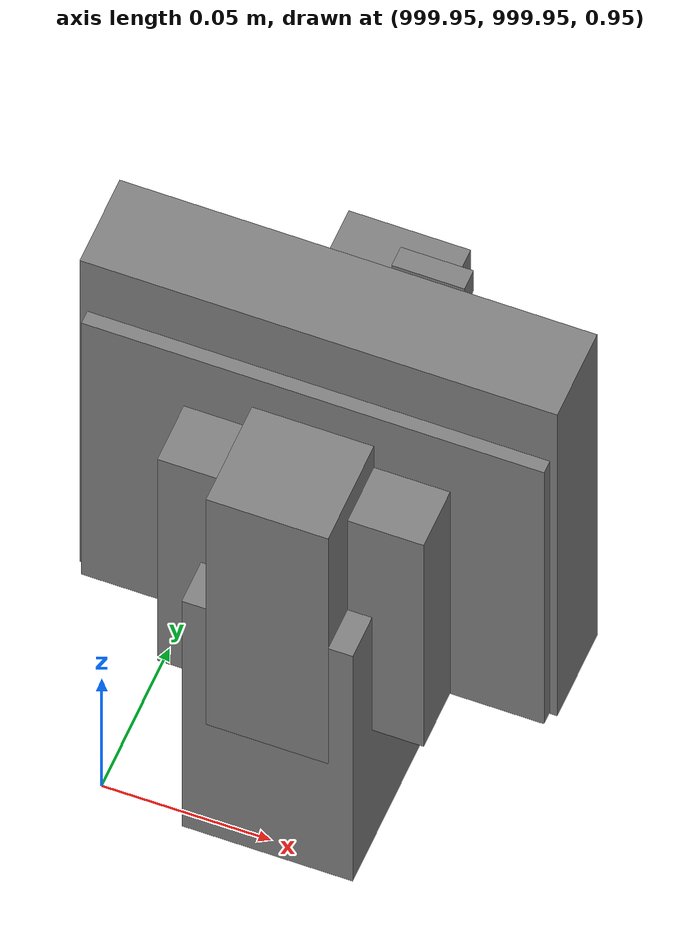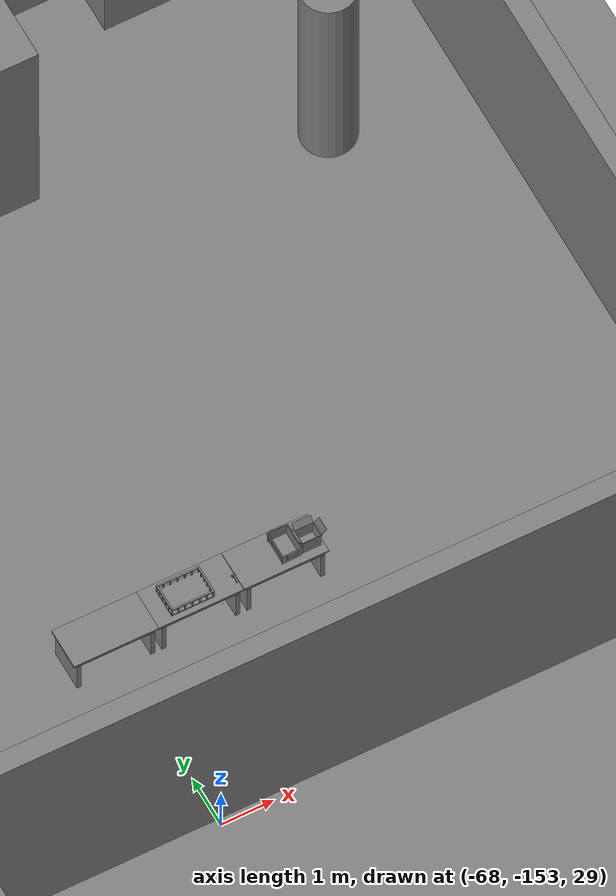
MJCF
<mujoco>
    <option gravity="0.000000000 0.000000000 -9.810000420" timestep="0.0049999999" integrator="implicitfast" density="1.225" viscosity="1.8000001e-05" noslip_iterations="10" iterations="100" sdf_iterations="50">
        <flag multiccd="disable"/>
    </option>
    <size memory="1000M"/>
    <compiler coordinate="local"/>
    <worldbody>
        <light cutoff="30" pos="0 1 1" dir="0 -1 -2"/>
        <light cutoff="30" pos="0 -1 1" dir="0 1 -2"/>
        <body pos="1000.000000000 1000.000000000 1.000000000" euler="0.000000000 0.000000000 180.000000000" name="openloong_gripper_2f85_fix_base_usda_wifi_box">
            <geom contype="1" conaffinity="1" density="1000" type="box" material="" rgba="0.500000000 0.500000000 0.500000000 1.000000000" solimp="0.899999976 0.949999988 0.001000000" friction="1.000000000 0.005000000 0.000100000" solref="0.020000000 1.000000000" margin="0" condim="3" group="0" pos="0.000000000 0.000000000 0.058978677" quat="0.000000000 0.000000047 0.000000000 1.000000000" size="0.068499997 0.018999999 0.059000000" name="openloong_gripper_2f85_fix_base_usda_geom_24C496CC_FD46_472F_80A8_6E0BBDEAA620"/>
            <freejoint name="openloong_gripper_2f85_fix_base_usda_wifi_box_joint"/>
            <site size="0.005000000 0.005000000 0.005000000" rgba="0.500000000 0.500000000 0.500000000 1.000000000" pos="0.000000000 0.000000000 0.000000000" quat="0.999961913 0.008726500 0.000000000 0.000000000" group="0" type="sphere" name="openloong_gripper_2f85_fix_base_usda_wifi_boxsite"/>
        </body>
        <body pos="1000.000000000 1000.000000000 1.000000000" euler="0.000000000 0.000000000 180.000000000" name="openloong_gripper_2f85_fix_base_usda_cpu_fan">
            <geom contype="1" conaffinity="1" density="1000" type="box" material="" rgba="0.500000000 0.500000000 0.500000000 1.000000000" solimp="0.899999976 0.949999988 0.001000000" friction="1.000000000 0.005000000 0.000100000" solref="0.020000000 1.000000000" margin="0" condim="3" group="0" pos="0.000000000 0.000000000 0.070034981" quat="0.000000000 0.000000000 0.000000000 1.000000000" size="0.070700005 0.014699999 0.070700005" name="openloong_gripper_2f85_fix_base_usda_geom_D772E4E7_FB12_4957_9AF6_75ABE6F2FC4A"/>
            <freejoint name="openloong_gripper_2f85_fix_base_usda_cpu_fan_joint"/>
            <site size="0.005000000 0.005000000 0.005000000" rgba="0.500000000 0.500000000 0.500000000 1.000000000" pos="0.000000000 0.000000000 0.000000000" quat="0.999961913 0.008726535 0.000000000 0.000000000" group="0" type="sphere" name="openloong_gripper_2f85_fix_base_usda_cpu_fancsite"/>
        </body>
        <body pos="1000.000000000 1000.000000000 1.000000000" euler="0.000000000 0.000000000 180.000000000" name="openloong_gripper_2f85_fix_base_usda_battery_01">
            <geom contype="1" conaffinity="1" density="1000" type="box" material="" rgba="0.500000000 0.500000000 0.500000000 1.000000000" solimp="0.899999976 0.949999988 0.001000000" friction="1.000000000 0.005000000 0.000100000" solref="0.020000000 1.000000000" margin="0" condim="3" group="0" pos="-0.011123657 -0.041940309 0.101691343" quat="1.000000000 0.000000000 0.000000000 0.000000000" size="0.010800000 0.003375000 0.004725000" name="openloong_gripper_2f85_fix_base_usda_geom_607BE3C6_7190_4C79_913C_226D8B04029A"/>
            <geom contype="1" conaffinity="1" density="1000" type="box" material="" rgba="0.500000000 0.500000000 0.500000000 1.000000000" solimp="0.899999976 0.949999988 0.001000000" friction="1.000000000 0.005000000 0.000100000" solref="0.020000000 1.000000000" margin="0" condim="3" group="0" pos="-0.010876465 -0.044247437 0.047066893" quat="0.998702705 -0.050920475 0.000000000 0.000000000" size="0.009450001 0.002700000 0.024975000" name="openloong_gripper_2f85_fix_base_usda_geom_83EFAA5B_D03F_411E_A803_B18BB57E58FF"/>
            <geom contype="1" conaffinity="1" density="1000" type="box" material="" rgba="0.500000000 0.500000000 0.500000000 1.000000000" solimp="0.899999976 0.949999988 0.001000000" friction="1.000000000 0.005000000 0.000100000" solref="0.020000000 1.000000000" margin="0" condim="3" group="0" pos="-0.001235962 -0.000659180 0.047381196" quat="1.000000000 0.000000000 0.000000000 0.000000000" size="0.039420001 0.039150000 0.047250003" name="openloong_gripper_2f85_fix_base_usda_geom_83D4BB5C_8E04_4B81_99D2_6ED0A23EA094"/>
            <geom contype="1" conaffinity="1" density="1000" type="box" material="" rgba="0.500000000 0.500000000 0.500000000 1.000000000" solimp="0.899999976 0.949999988 0.001000000" friction="1.000000000 0.005000000 0.000100000" solref="0.020000000 1.000000000" margin="0" condim="3" group="0" pos="-0.010876465 -0.039138794 0.009851727" quat="1.000000000 0.000000000 0.000000000 0.000000000" size="0.009450001 0.010800000 0.013500000" name="openloong_gripper_2f85_fix_base_usda_geom_C21D43B4_AB9F_4C74_BDED_2F3DD93660F6"/>
            <geom contype="1" conaffinity="1" density="1000" type="box" material="" rgba="0.500000000 0.500000000 0.500000000 1.000000000" solimp="0.899999976 0.949999988 0.001000000" friction="1.000000000 0.005000000 0.000100000" solref="0.020000000 1.000000000" margin="0" condim="3" group="0" pos="-0.010876465 -0.041528322 0.071508206" quat="1.000000000 0.000000000 0.000000000 0.000000000" size="0.009450001 0.002700000 0.027000001" name="openloong_gripper_2f85_fix_base_usda_geom_2BA849AF_431E_4450_B3E0_5BFA9027CE38"/>
            <freejoint name="openloong_gripper_2f85_fix_base_usda_battery_01_joint"/>
            <site size="0.005000000 0.005000000 0.005000000" rgba="0.500000000 0.500000000 0.500000000 1.000000000" pos="0.000000000 0.000000000 0.000000000" quat="0.999961913 0.008726500 0.000000000 0.000000000" group="0" type="sphere" name="openloong_gripper_2f85_fix_base_usda_battery_01site"/>
        </body>
        <body pos="-66.028076172 -149.721923828 31.167173386" euler="-88.323692322 1.175059319 147.956604004" mocap="true" name="spotlight5_SpotLight"/>
        <body pos="1000.000000000 1000.000000000 1.000000000" euler="0.000011953 0.000005123 -179.999984741" name="openloong_gripper_2f85_fix_base_usda_intel_box">
            <geom contype="1" conaffinity="1" density="1000" type="box" material="" rgba="0.500000000 0.500000000 0.500000000 1.000000000" solimp="0.899999976 0.949999988 0.001000000" friction="1.000000000 0.005000000 0.000100000" solref="0.020000000 1.000000000" margin="0" condim="3" group="0" pos="0.000000000 -0.000067139 0.000082284" quat="0.707106709 0.000000225 0.000000253 0.707106650" size="0.052800003 0.025300000 0.052800003" name="openloong_gripper_2f85_fix_base_usda_geom_BC74EB51_D357_46E8_8332_4EFFC6821114"/>
            <freejoint name="openloong_gripper_2f85_fix_base_usda_intel_box_joint"/>
            <site size="0.005000000 0.005000000 0.005000000" rgba="0.500000000 0.500000000 0.500000000 1.000000000" pos="0.000000000 0.000000000 0.000000000" quat="0.999961913 0.008726500 0.000000000 0.000000000" group="0" type="sphere" name="openloong_gripper_2f85_fix_base_usda_intel_boxsite"/>
        </body>
        <body pos="1000.000000000 999.999938965 1.000000000" euler="0.000000000 0.000000000 180.000000000" name="openloong_gripper_2f85_fix_base_usda_intelcore_i5">
            <geom contype="1" conaffinity="1" density="1000" type="box" material="" rgba="0.500000000 0.500000000 0.500000000 1.000000000" solimp="0.899999976 0.949999988 0.001000000" friction="1.000000000 0.005000000 0.000100000" solref="0.020000000 1.000000000" margin="0" condim="3" group="0" pos="0.000000000 0.000000000 0.051722717" quat="0.707106709 0.000000000 0.000000000 -0.707106769" size="0.052800000 0.018080002 0.052800000" name="openloong_gripper_2f85_fix_base_usda_geom_73CB9262_ADD6_4E87_843D_8BA5AD3E99FF"/>
            <freejoint name="openloong_gripper_2f85_fix_base_usda_intelcore_i5_joint"/>
            <site size="0.005000000 0.005000000 0.005000000" rgba="0.500000000 0.500000000 0.500000000 1.000000000" pos="0.000000000 0.000000000 0.000000000" quat="0.999961913 0.008726534 0.000000000 0.000000000" group="0" type="sphere" name="openloong_gripper_2f85_fix_base_usda_intelcore_i5site"/>
        </body>
        <body pos="-66.156936646 -149.096420288 31.162014008" euler="153.378692627 -17.041828156 -144.125793457" mocap="true" name="spotlight1_SpotLight"/>
        <body pos="-66.002487183 -149.595169067 31.170478821" euler="12.105177879 -86.053436279 47.515045166" mocap="true" name="spotlight4_SpotLight"/>
        <body pos="-64.866622925 -149.383972168 30.183746338" euler="89.999984741 89.999946594 0.000000000" name="openloong_gripper_2f85_fix_base_usda_bluebox_01">
            <geom contype="1" conaffinity="1" density="1000" type="box" material="" rgba="0.500000000 0.500000000 0.500000000 1.000000000" solimp="0.899999976 0.949999988 0.001000000" friction="1.000000000 0.005000000 0.000100000" solref="0.020000000 1.000000000" margin="0" condim="3" group="0" pos="0.276580811 0.187225342 0.000068665" quat="0.707106948 0.000077471 0.707106352 0.000077486" size="0.100000001 0.057999998 0.010000000" name="openloong_gripper_2f85_fix_base_usda_geom_049DE205_8718_4F42_BB54_34D98DB1EB62"/>
            <geom contype="1" conaffinity="1" density="1000" type="box" material="" rgba="0.500000000 0.500000000 0.500000000 1.000000000" solimp="0.899999976 0.949999988 0.001000000" friction="1.000000000 0.005000000 0.000100000" solref="0.020000000 1.000000000" margin="0" condim="3" group="0" pos="0.000000000 0.002883911 0.000000000" quat="0.999999881 0.000000000 0.000000000 0.000000000" size="0.254000008 0.003000000 0.172000006" name="openloong_gripper_2f85_fix_base_usda_geom_2B580183_120B_43B4_AD38_6B4E223EF658"/>
            <geom contype="1" conaffinity="1" density="1000" type="box" material="" rgba="0.500000000 0.500000000 0.500000000 1.000000000" solimp="0.899999976 0.949999988 0.001000000" friction="1.000000000 0.005000000 0.000100000" solref="0.020000000 1.000000000" margin="0" condim="3" group="0" pos="0.000000000 0.124874115 0.173484802" quat="0.999796331 0.020176515 -0.000000015 0.000000030" size="0.259999990 0.119999997 0.007000000" name="openloong_gripper_2f85_fix_base_usda_geom_E1E1DEDF_3764_493F_BAE6_09E9567F3637"/>
            <geom contype="1" conaffinity="1" density="1000" type="box" material="" rgba="0.500000000 0.500000000 0.500000000 1.000000000" solimp="0.899999976 0.949999988 0.001000000" friction="1.000000000 0.005000000 0.000100000" solref="0.020000000 1.000000000" margin="0" condim="3" group="0" pos="0.000000000 0.124874115 -0.173469543" quat="0.999796331 -0.020176545 -0.000000015 0.000000000" size="0.259999990 0.119999997 0.007000000" name="openloong_gripper_2f85_fix_base_usda_geom_715C5CF9_1275_4D9F_A554_EFBF317F4CE5"/>
            <geom contype="1" conaffinity="1" density="1000" type="box" material="" rgba="0.500000000 0.500000000 0.500000000 1.000000000" solimp="0.899999976 0.949999988 0.001000000" friction="1.000000000 0.005000000 0.000100000" solref="0.020000000 1.000000000" margin="0" condim="3" group="0" pos="0.000000000 0.214008331 0.188980103" quat="0.999912977 0.013176724 0.000000015 0.000000000" size="0.259999990 0.029999999 0.012500000" name="openloong_gripper_2f85_fix_base_usda_geom_09CD64E7_5867_4416_9162_8886F974E439"/>
            <geom contype="1" conaffinity="1" density="1000" type="box" material="" rgba="0.500000000 0.500000000 0.500000000 1.000000000" solimp="0.899999976 0.949999988 0.001000000" friction="1.000000000 0.005000000 0.000100000" solref="0.020000000 1.000000000" margin="0" condim="3" group="0" pos="-0.258361816 0.125289917 0.001876831" quat="0.702796936 -0.020792112 0.710783124 0.020769298" size="0.189999998 0.119999997 0.009000000" name="openloong_gripper_2f85_fix_base_usda_geom_E1152B5D_AEB9_4A6A_8598_46441E99E53F"/>
            <geom contype="1" conaffinity="1" density="1000" type="box" material="" rgba="0.500000000 0.500000000 0.500000000 1.000000000" solimp="0.899999976 0.949999988 0.001000000" friction="1.000000000 0.005000000 0.000100000" solref="0.020000000 1.000000000" margin="0" condim="3" group="0" pos="0.000000000 0.214008331 -0.188980103" quat="0.999912977 -0.013176769 0.000000030 0.000000015" size="0.259999990 0.029999999 0.012500000" name="openloong_gripper_2f85_fix_base_usda_geom_94E681DB_DA86_4307_9977_06FC38129E4F"/>
            <geom contype="1" conaffinity="1" density="1000" type="box" material="" rgba="0.500000000 0.500000000 0.500000000 1.000000000" solimp="0.899999976 0.949999988 0.001000000" friction="1.000000000 0.005000000 0.000100000" solref="0.020000000 1.000000000" margin="0" condim="3" group="0" pos="-0.276611328 0.187225342 0.000068665" quat="0.707106650 0.000077441 0.707106709 0.000077456" size="0.100000001 0.057999998 0.010000000" name="openloong_gripper_2f85_fix_base_usda_geom_671B1AE7_AE75_4E6E_A4CE_6749303C8512"/>
            <geom contype="1" conaffinity="1" density="1000" type="box" material="" rgba="0.500000000 0.500000000 0.500000000 1.000000000" solimp="0.899999976 0.949999988 0.001000000" friction="1.000000000 0.005000000 0.000100000" solref="0.020000000 1.000000000" margin="0" condim="3" group="0" pos="0.258331299 0.125289917 0.001876831" quat="0.702851415 0.018856421 0.710823774 -0.019329369" size="0.189999998 0.119999997 0.009000000" name="openloong_gripper_2f85_fix_base_usda_geom_BF97913C_9B4F_43FD_A4C8_F21D1F0AFF5A"/>
            <freejoint name="openloong_gripper_2f85_fix_base_usda_bluebox_01_joint"/>
            <site size="0.005000000 0.005000000 0.005000000" rgba="0.500000000 0.500000000 0.500000000 1.000000000" pos="0.000000000 0.000000000 0.000000000" quat="0.999961913 0.008726534 0.000000000 0.000000000" group="0" type="sphere" name="openloong_gripper_2f85_fix_base_usda_bluebox_01site"/>
        </body>
        <body pos="-64.496299744 -149.491867065 30.235729218" euler="0.000000000 0.000000000 89.999946594" name="openloong_gripper_2f85_fix_base_usda_cardboardbox_01">
            <geom contype="1" conaffinity="1" density="1000" type="box" material="" rgba="0.500000000 0.500000000 0.500000000 1.000000000" solimp="0.899999976 0.949999988 0.001000000" friction="1.000000000 0.005000000 0.000100000" solref="0.020000000 1.000000000" margin="0" condim="3" group="0" pos="-0.003166199 -0.004086494 0.005052090" quat="1.000000000 0.000000000 0.000000000 0.000000000" size="0.142499998 0.177500010 0.005000000" name="openloong_gripper_2f85_fix_base_usda_geom_AD35096C_49FB_4A88_BBCC_FEA6772747A3"/>
            <geom contype="1" conaffinity="1" density="1000" type="box" material="" rgba="0.500000000 0.500000000 0.500000000 1.000000000" solimp="0.899999976 0.949999988 0.001000000" friction="1.000000000 0.005000000 0.000100000" solref="0.020000000 1.000000000" margin="0" condim="3" group="0" pos="-0.003166199 0.170316696 0.150570869" quat="1.000000000 0.000000000 0.000000000 0.000000000" size="0.142499998 0.005000000 0.149999991" name="openloong_gripper_2f85_fix_base_usda_geom_63CCA8D1_FA3E_439E_9554_86A6777ADEE7"/>
            <geom contype="1" conaffinity="1" density="1000" type="box" material="" rgba="0.500000000 0.500000000 0.500000000 1.000000000" solimp="0.899999976 0.949999988 0.001000000" friction="1.000000000 0.005000000 0.000100000" solref="0.020000000 1.000000000" margin="0" condim="3" group="0" pos="-0.147399902 -0.005307198 0.150570869" quat="1.000000000 0.000000000 0.000000000 0.000000000" size="0.005000000 0.177500010 0.149999991" name="openloong_gripper_2f85_fix_base_usda_geom_9DC86262_282D_4208_868B_2689C365C2CB"/>
            <geom contype="1" conaffinity="1" density="1000" type="box" material="" rgba="0.500000000 0.500000000 0.500000000 1.000000000" solimp="0.899999976 0.949999988 0.001000000" friction="1.000000000 0.005000000 0.000100000" solref="0.020000000 1.000000000" margin="0" condim="3" group="0" pos="0.140275955 -0.005307198 0.150570869" quat="1.000000000 0.000000000 0.000000000 0.000000000" size="0.005000000 0.177500010 0.149999991" name="openloong_gripper_2f85_fix_base_usda_geom_397BF4DC_54F6_4876_939E_8DEACD3C2531"/>
            <geom contype="1" conaffinity="1" density="1000" type="box" material="" rgba="0.500000000 0.500000000 0.500000000 1.000000000" solimp="0.899999976 0.949999988 0.001000000" friction="1.000000000 0.005000000 0.000100000" solref="0.020000000 1.000000000" margin="0" condim="3" group="0" pos="-0.003166199 -0.181550980 0.150570869" quat="1.000000000 0.000000000 0.000000000 0.000000000" size="0.142499998 0.005000000 0.149999991" name="openloong_gripper_2f85_fix_base_usda_geom_98E0B8DB_A38A_477F_88D1_7F0FBD94C13E"/>
            <freejoint name="openloong_gripper_2f85_fix_base_usda_cardboardbox_01_joint"/>
            <site size="0.005000000 0.005000000 0.005000000" rgba="0.500000000 0.500000000 0.500000000 1.000000000" pos="0.000000000 0.000000000 0.000000000" quat="0.999961913 0.008726535 0.000000000 0.000000000" group="0" type="sphere" name="openloong_gripper_2f85_fix_base_usda_site_E2A55174_D6A1_41A2_B273_C0F6614773A2"/>
            <body pos="0.139160156 -0.004048347 0.301930904" euler="-179.999954224 49.383502960 179.999954224" name="openloong_gripper_2f85_fix_base_usda_A1_006">
                <geom contype="1" conaffinity="1" density="1000" type="box" material="" rgba="0.500000000 0.500000000 0.500000000 1.000000000" solimp="0.899999976 0.949999988 0.001000000" friction="1.000000000 0.005000000 0.000100000" solref="0.020000000 1.000000000" margin="0" condim="3" group="0" pos="-0.071587563 0.000009537 0.001745224" quat="0.999999881 0.000000000 0.000000000 0.000000000" size="0.071249999 0.179999992 0.002500000" name="openloong_gripper_2f85_fix_base_usda_geom_DAFED99C_1231_49AA_B34C_8D631AC3B80F"/>
                <joint armature="0" stiffness="0.07" damping="0.0099999998" axis="0.000000 1.000000 0.000000" type="hinge" name="openloong_gripper_2f85_fix_base_usda_A1_006"/>
            </body>
            <body pos="-0.145902634 -0.004086494 0.301938057" euler="-180.000000000 -60.000011444 -180.000000000" name="openloong_gripper_2f85_fix_base_usda_A2_006">
                <geom contype="1" conaffinity="1" density="1000" type="box" material="" rgba="0.500000000 0.500000000 0.500000000 1.000000000" solimp="0.899999976 0.949999988 0.001000000" friction="1.000000000 0.005000000 0.000100000" solref="0.020000000 1.000000000" margin="0" condim="3" group="0" pos="0.071268082 0.000009537 0.002717972" quat="0.000002921 0.000000000 -0.000000030 0.999999881" size="0.071249999 0.179999992 0.002500000" name="openloong_gripper_2f85_fix_base_usda_geom_0AEB1B77_5197_47AE_8A3D_7E1C085737D3"/>
                <joint armature="0" stiffness="0.07" damping="0.0099999998" axis="0.000000 1.000000 0.000000" type="hinge" name="openloong_gripper_2f85_fix_base_usda_A2_006"/>
            </body>
            <body pos="-0.003385544 0.175991058 0.301930904" euler="-125.858116150 -0.000004561 0.000002331" name="openloong_gripper_2f85_fix_base_usda_B2_006">
                <geom contype="1" conaffinity="1" density="1000" type="box" material="" rgba="0.500000000 0.500000000 0.500000000 1.000000000" solimp="0.899999976 0.949999988 0.001000000" friction="1.000000000 0.005000000 0.000100000" solref="0.020000000 1.000000000" margin="0" condim="3" group="0" pos="0.000009537 -0.070939064 -0.002470016" quat="0.999614120 0.027776197 -0.000000015 0.000000030" size="0.137500003 0.064999998 0.005000000" name="openloong_gripper_2f85_fix_base_usda_geom_B4162CEA_2E81_48A6_ADC9_1E40E581057E"/>
                <joint armature="0" stiffness="0.07" damping="0.0099999998" axis="1.000000 0.000000 0.000000" type="hinge" name="openloong_gripper_2f85_fix_base_usda_B2_006"/>
            </body>
            <body pos="-0.003385544 -0.184140205 0.301938057" euler="147.805557251 0.000000000 0.000000000" name="openloong_gripper_2f85_fix_base_usda_B1_006">
                <geom contype="1" conaffinity="1" density="1000" type="box" material="" rgba="0.500000000 0.500000000 0.500000000 1.000000000" solimp="0.899999976 0.949999988 0.001000000" friction="1.000000000 0.005000000 0.000100000" solref="0.020000000 1.000000000" margin="0" condim="3" group="0" pos="-0.000028610 0.070202351 -0.002703667" quat="0.999614179 -0.027776167 0.000000000 0.000000000" size="0.137500003 0.064999998 0.005000000" name="openloong_gripper_2f85_fix_base_usda_geom_2565C61E_9BA8_4F89_BDC0_1C4629884168"/>
                <joint armature="0" stiffness="0.07" damping="0.0099999998" axis="1.000000 0.000000 0.000000" type="hinge" name="openloong_gripper_2f85_fix_base_usda_B1_006"/>
            </body>
        </body>
        <body pos="-65.882858276 -149.481979370 30.229999542" euler="-64.487716675 0.000000000 0.000000000" name="openloong_gripper_2f85_fix_base_usda_Barcode">
            <geom contype="1" conaffinity="1" density="1000" type="box" material="" rgba="0.500000000 0.500000000 0.500000000 1.000000000" solimp="0.899999976 0.949999988 0.001000000" friction="1.000000000 0.005000000 0.000100000" solref="0.020000000 1.000000000" margin="0" condim="3" group="0" pos="0.000000000 0.013038635 0.001419067" quat="0.000000000 0.000000000 0.000000000 1.000000119" size="0.034000002 0.010000000 0.017999999" name="openloong_gripper_2f85_fix_base_usda_geom_5D36E76F_2D98_4636_BE5E_080F522EBE93"/>
            <geom contype="1" conaffinity="1" density="1000" type="box" material="" rgba="0.500000000 0.500000000 0.500000000 1.000000000" solimp="0.899999976 0.949999988 0.001000000" friction="1.000000000 0.005000000 0.000100000" solref="0.020000000 1.000000000" margin="0" condim="3" group="0" pos="0.000000000 -0.035301208 -0.007095337" quat="0.000000000 0.000000000 -0.043619365 0.999048233" size="0.028999999 0.010000000 0.020000000" name="openloong_gripper_2f85_fix_base_usda_geom_AFCA4043_D994_49F3_BF58_F89902F7B0CF"/>
            <geom contype="1" conaffinity="1" density="1000" type="box" material="" rgba="0.500000000 0.500000000 0.500000000 1.000000000" solimp="0.899999976 0.949999988 0.001000000" friction="1.000000000 0.005000000 0.000100000" solref="0.020000000 1.000000000" margin="0" condim="3" group="0" pos="0.000000000 -0.043411255 -0.011749268" quat="0.922262907 0.386563420 0.000000000 0.000000000" size="0.026000001 0.010000000 0.020000000" name="openloong_gripper_2f85_fix_base_usda_geom_6752F675_F616_4D8D_BC28_CE16B89EE5DA"/>
            <geom contype="1" conaffinity="1" density="1000" type="box" material="" rgba="0.500000000 0.500000000 0.500000000 1.000000000" solimp="0.899999976 0.949999988 0.001000000" friction="1.000000000 0.005000000 0.000100000" solref="0.020000000 1.000000000" margin="0" condim="3" group="0" pos="0.000000000 -0.016967773 -0.031860352" quat="0.000000000 0.000000000 0.000000000 1.000000119" size="0.008000000 0.010000000 0.013000000" name="openloong_gripper_2f85_fix_base_usda_geom_D74ADB05_6E8B_427E_9456_DBD30C8423CE"/>
            <geom contype="1" conaffinity="1" density="1000" type="box" material="" rgba="0.500000000 0.500000000 0.500000000 1.000000000" solimp="0.899999976 0.949999988 0.001000000" friction="1.000000000 0.005000000 0.000100000" solref="0.020000000 1.000000000" margin="0" condim="3" group="0" pos="0.000000000 -0.001869202 0.000312805" quat="0.953716993 0.300705761 0.000000000 0.000000000" size="0.032000002 0.010000000 0.018999999" name="openloong_gripper_2f85_fix_base_usda_geom_D959E53E_C90A_4C1B_B09D_37C53E814682"/>
            <geom contype="1" conaffinity="1" density="1000" type="box" material="" rgba="0.500000000 0.500000000 0.500000000 1.000000000" solimp="0.899999976 0.949999988 0.001000000" friction="1.000000000 0.005000000 0.000100000" solref="0.020000000 1.000000000" margin="0" condim="3" group="0" pos="0.000000000 -0.019531250 -0.003173828" quat="0.953716993 0.300705761 0.000000000 0.000000000" size="0.030999999 0.010000000 0.020000000" name="openloong_gripper_2f85_fix_base_usda_geom_6F7CADAC_DCB0_40D5_8154_AE6491CCB919"/>
            <geom contype="1" conaffinity="1" density="1000" type="box" material="" rgba="0.500000000 0.500000000 0.500000000 1.000000000" solimp="0.899999976 0.949999988 0.001000000" friction="1.000000000 0.005000000 0.000100000" solref="0.020000000 1.000000000" margin="0" condim="3" group="0" pos="0.000000000 -0.035301208 -0.007095337" quat="0.953716993 0.300705761 0.000000000 0.000000000" size="0.028999999 0.010000000 0.020000000" name="openloong_gripper_2f85_fix_base_usda_geom_55272722_35E6_4ABB_8006_559D267B1025"/>
            <geom contype="1" conaffinity="1" density="1000" type="box" material="" rgba="0.500000000 0.500000000 0.500000000 1.000000000" solimp="0.899999976 0.949999988 0.001000000" friction="1.000000000 0.005000000 0.000100000" solref="0.020000000 1.000000000" margin="0" condim="3" group="0" pos="0.000000000 -0.042617798 -0.071121216" quat="0.000000000 0.000000000 0.000000000 1.000000119" size="0.013000000 0.021000000 0.059999999" name="openloong_gripper_2f85_fix_base_usda_geom_A7495DDA_4B57_40AD_92B7_2A2ED7BDEDD8"/>
            <freejoint name="openloong_gripper_2f85_fix_base_usda_Barcode_joint"/>
            <site size="0.005000000 0.005000000 0.005000000" rgba="0.500000000 0.500000000 0.500000000 1.000000000" pos="0.000000000 0.000000000 0.000000000" quat="1.000000000 0.000000000 0.000000000 0.000000000" group="0" type="sphere" name="openloong_gripper_2f85_fix_base_usda_Barcode_site"/>
        </body>
        <body pos="-66.745018005 -149.392349243 30.184000015" euler="0.000000000 0.000000000 89.999946594" name="[22331550298096]_Basket_01">
            <geom contype="1" conaffinity="1" density="1000" type="box" material="" rgba="0.500000000 0.500000000 0.500000000 1.000000000" solimp="0.899999976 0.949999988 0.001000000" friction="1.000000000 0.005000000 0.000100000" solref="0.020000000 1.000000000" margin="0" condim="3" group="0" pos="-0.052425385 0.389207840 0.089787483" quat="0.707107008 0.000000000 0.000000000 0.707106411" size="0.014249999 0.014249999 0.059999999" name="[22331550298096]_geom_4E6438E3_42EF_4B99_A30E_6DEAB6A64E70"/>
            <geom contype="1" conaffinity="1" density="1000" type="box" material="" rgba="0.500000000 0.500000000 0.500000000 1.000000000" solimp="0.899999976 0.949999988 0.001000000" friction="1.000000000 0.005000000 0.000100000" solref="0.020000000 1.000000000" margin="0" condim="3" group="0" pos="0.264015198 -0.133043289 0.089787483" quat="0.707107008 0.000000000 0.000000000 0.707106411" size="0.014249999 0.014249999 0.059999999" name="[22331550298096]_geom_95C16B29_8AD2_47FB_81F0_94F260323CBD"/>
            <geom contype="1" conaffinity="1" density="1000" type="box" material="" rgba="0.500000000 0.500000000 0.500000000 1.000000000" solimp="0.899999976 0.949999988 0.001000000" friction="1.000000000 0.005000000 0.000100000" solref="0.020000000 1.000000000" margin="0" condim="3" group="0" pos="-0.264015198 -0.265548706 0.089793205" quat="0.707107008 0.000000000 0.000000000 0.707106411" size="0.014249999 0.014249999 0.059999999" name="[22331550298096]_geom_47F017CE_B0A5_4E2E_8247_E72B36FE6B48"/>
            <geom contype="1" conaffinity="1" density="1000" type="box" material="" rgba="0.500000000 0.500000000 0.500000000 1.000000000" solimp="0.899999976 0.949999988 0.001000000" friction="1.000000000 0.005000000 0.000100000" solref="0.020000000 1.000000000" margin="0" condim="3" group="0" pos="-0.160263062 -0.389322281 0.089793205" quat="0.707107008 0.000000000 0.000000000 0.707106411" size="0.014249999 0.014249999 0.059999999" name="[22331550298096]_geom_BED8B42B_1212_42FE_95B0_1233505E8970"/>
            <geom contype="1" conaffinity="1" density="1000" type="box" material="" rgba="0.500000000 0.500000000 0.500000000 1.000000000" solimp="0.899999976 0.949999988 0.001000000" friction="1.000000000 0.005000000 0.000100000" solref="0.020000000 1.000000000" margin="0" condim="3" group="0" pos="0.162265778 -0.389322281 0.089787483" quat="0.707107008 0.000000000 0.000000000 0.707106411" size="0.014249999 0.014249999 0.059999999" name="[22331550298096]_geom_FFDC7BF0_0A5C_4786_B4E0_5B3C7357EF69"/>
            <geom contype="1" conaffinity="1" density="1000" type="box" material="" rgba="0.500000000 0.500000000 0.500000000 1.000000000" solimp="0.899999976 0.949999988 0.001000000" friction="1.000000000 0.005000000 0.000100000" solref="0.020000000 1.000000000" margin="0" condim="3" group="0" pos="0.264015198 0.389207840 0.089787483" quat="0.707107008 0.000000000 0.000000000 0.707106411" size="0.014249999 0.014249999 0.059999999" name="[22331550298096]_geom_71916D65_7005_4F19_9BBC_E6A7668A9263"/>
            <geom contype="1" conaffinity="1" density="1000" type="box" material="" rgba="0.500000000 0.500000000 0.500000000 1.000000000" solimp="0.899999976 0.949999988 0.001000000" friction="1.000000000 0.005000000 0.000100000" solref="0.020000000 1.000000000" margin="0" condim="3" group="0" pos="-0.264015198 -0.133043289 0.089793205" quat="0.707107008 0.000000000 0.000000000 0.707106411" size="0.014249999 0.014249999 0.059999999" name="[22331550298096]_geom_17BDBB59_76D0_434F_A609_443945E5B3F2"/>
            <geom contype="1" conaffinity="1" density="1000" type="box" material="" rgba="0.500000000 0.500000000 0.500000000 1.000000000" solimp="0.899999976 0.949999988 0.001000000" friction="1.000000000 0.005000000 0.000100000" solref="0.020000000 1.000000000" margin="0" condim="3" group="0" pos="-0.264026642 0.269256592 0.089793205" quat="0.707107008 0.000000000 0.000000000 0.707106411" size="0.014249999 0.014249999 0.059999999" name="[22331550298096]_geom_84C8D153_BDBA_48C0_8360_DC148005FBE5"/>
            <geom contype="1" conaffinity="1" density="1000" type="box" material="" rgba="0.500000000 0.500000000 0.500000000 1.000000000" solimp="0.899999976 0.949999988 0.001000000" friction="1.000000000 0.005000000 0.000100000" solref="0.020000000 1.000000000" margin="0" condim="3" group="0" pos="0.054462433 0.389207840 0.089787483" quat="0.707107008 0.000000000 0.000000000 0.707106411" size="0.014249999 0.014249999 0.059999999" name="[22331550298096]_geom_6FA4A3C0_3D50_47BF_A311_4B39FF1B1775"/>
            <geom contype="1" conaffinity="1" density="1000" type="box" material="" rgba="0.500000000 0.500000000 0.500000000 1.000000000" solimp="0.899999976 0.949999988 0.001000000" friction="1.000000000 0.005000000 0.000100000" solref="0.020000000 1.000000000" margin="0" condim="3" group="0" pos="0.054462433 -0.389322281 0.089787483" quat="0.707107008 0.000000000 0.000000000 0.707106411" size="0.014249999 0.014249999 0.059999999" name="[22331550298096]_geom_AA687730_5034_46A4_8924_5D504448C979"/>
            <geom contype="1" conaffinity="1" density="1000" type="box" material="" rgba="0.500000000 0.500000000 0.500000000 1.000000000" solimp="0.899999976 0.949999988 0.001000000" friction="1.000000000 0.005000000 0.000100000" solref="0.020000000 1.000000000" margin="0" condim="3" group="0" pos="0.264015198 0.269256592 0.089793205" quat="0.707107008 0.000000000 0.000000000 0.707106411" size="0.014249999 0.014249999 0.059999999" name="[22331550298096]_geom_F4965FB4_9597_444C_BEFC_4C10A80F295C"/>
            <geom contype="1" conaffinity="1" density="1000" type="box" material="" rgba="0.500000000 0.500000000 0.500000000 1.000000000" solimp="0.899999976 0.949999988 0.001000000" friction="1.000000000 0.005000000 0.000100000" solref="0.020000000 1.000000000" margin="0" condim="3" group="0" pos="0.264015198 -0.389322281 0.089787483" quat="0.707107008 0.000000000 0.000000000 0.707106411" size="0.014249999 0.014249999 0.059999999" name="[22331550298096]_geom_4B9D55D8_3642_48D7_8277_A8F714045D84"/>
            <geom contype="1" conaffinity="1" density="1000" type="box" material="" rgba="0.500000000 0.500000000 0.500000000 1.000000000" solimp="0.899999976 0.949999988 0.001000000" friction="1.000000000 0.005000000 0.000100000" solref="0.020000000 1.000000000" margin="0" condim="3" group="0" pos="0.000000000 0.000000000 0.015998840" quat="0.707107008 0.000000000 0.000000000 0.707106411" size="0.403499991 0.279000014 0.015750000" name="[22331550298096]_geom_A43E418A_D4DB_45C5_B766_34C2AEAA0D97"/>
            <geom contype="1" conaffinity="1" density="1000" type="box" material="" rgba="0.500000000 0.500000000 0.500000000 1.000000000" solimp="0.899999976 0.949999988 0.001000000" friction="1.000000000 0.005000000 0.000100000" solref="0.020000000 1.000000000" margin="0" condim="3" group="0" pos="0.000000000 -0.389476776 0.163619041" quat="0.707107008 0.000000000 0.000000000 0.707106411" size="0.015000000 0.277500004 0.015750000" name="[22331550298096]_geom_F6DB8F77_8ED1_4426_ACBA_C70E1157962D"/>
            <geom contype="1" conaffinity="1" density="1000" type="box" material="" rgba="0.500000000 0.500000000 0.500000000 1.000000000" solimp="0.899999976 0.949999988 0.001000000" friction="1.000000000 0.005000000 0.000100000" solref="0.020000000 1.000000000" margin="0" condim="3" group="0" pos="0.162265778 0.389207840 0.089787483" quat="0.707107008 0.000000000 0.000000000 0.707106411" size="0.014249999 0.014249999 0.059999999" name="[22331550298096]_geom_AB08CC9D_73BE_44AE_B355_155BA22CCCF0"/>
            <geom contype="1" conaffinity="1" density="1000" type="box" material="" rgba="0.500000000 0.500000000 0.500000000 1.000000000" solimp="0.899999976 0.949999988 0.001000000" friction="1.000000000 0.005000000 0.000100000" solref="0.020000000 1.000000000" margin="0" condim="3" group="0" pos="0.000000000 0.389471054 0.163619041" quat="0.707107008 0.000000000 0.000000000 0.707106411" size="0.015000000 0.277500004 0.015750000" name="[22331550298096]_geom_EA8CD241_5A8B_46FD_A335_E01B7A560CEA"/>
            <geom contype="1" conaffinity="1" density="1000" type="box" material="" rgba="0.500000000 0.500000000 0.500000000 1.000000000" solimp="0.899999976 0.949999988 0.001000000" friction="1.000000000 0.005000000 0.000100000" solref="0.020000000 1.000000000" margin="0" condim="3" group="0" pos="-0.263511658 0.000000000 0.163619041" quat="0.707107008 0.000000000 0.000000000 0.707106411" size="0.403499991 0.015000000 0.015750000" name="[22331550298096]_geom_D7E4C00F_0783_442C_9DB4_53B95E1E60B0"/>
            <geom contype="1" conaffinity="1" density="1000" type="box" material="" rgba="0.500000000 0.500000000 0.500000000 1.000000000" solimp="0.899999976 0.949999988 0.001000000" friction="1.000000000 0.005000000 0.000100000" solref="0.020000000 1.000000000" margin="0" condim="3" group="0" pos="-0.264015198 0.141334534 0.089793205" quat="0.707107008 0.000000000 0.000000000 0.707106411" size="0.014249999 0.014249999 0.059999999" name="[22331550298096]_geom_B5305D53_25E0_4321_96B0_416FA5F8118A"/>
            <geom contype="1" conaffinity="1" density="1000" type="box" material="" rgba="0.500000000 0.500000000 0.500000000 1.000000000" solimp="0.899999976 0.949999988 0.001000000" friction="1.000000000 0.005000000 0.000100000" solref="0.020000000 1.000000000" margin="0" condim="3" group="0" pos="0.264015198 -0.265548706 0.089787483" quat="0.707107008 0.000000000 0.000000000 0.707106411" size="0.014249999 0.014249999 0.059999999" name="[22331550298096]_geom_44E0631D_DC63_486C_85C8_45181124BCBA"/>
            <geom contype="1" conaffinity="1" density="1000" type="box" material="" rgba="0.500000000 0.500000000 0.500000000 1.000000000" solimp="0.899999976 0.949999988 0.001000000" friction="1.000000000 0.005000000 0.000100000" solref="0.020000000 1.000000000" margin="0" condim="3" group="0" pos="-0.160263062 0.389207840 0.089787483" quat="0.707107008 0.000000000 0.000000000 0.707106411" size="0.014249999 0.014249999 0.059999999" name="[22331550298096]_geom_6AC9DA15_7C58_476E_987D_9466A510141B"/>
            <geom contype="1" conaffinity="1" density="1000" type="box" material="" rgba="0.500000000 0.500000000 0.500000000 1.000000000" solimp="0.899999976 0.949999988 0.001000000" friction="1.000000000 0.005000000 0.000100000" solref="0.020000000 1.000000000" margin="0" condim="3" group="0" pos="-0.052425385 -0.389322281 0.089787483" quat="0.707107008 0.000000000 0.000000000 0.707106411" size="0.014249999 0.014249999 0.059999999" name="[22331550298096]_geom_26EADEA4_9F04_4204_B372_9A5E49F550DB"/>
            <geom contype="1" conaffinity="1" density="1000" type="box" material="" rgba="0.500000000 0.500000000 0.500000000 1.000000000" solimp="0.899999976 0.949999988 0.001000000" friction="1.000000000 0.005000000 0.000100000" solref="0.020000000 1.000000000" margin="0" condim="3" group="0" pos="-0.264026642 -0.389322281 0.089793205" quat="0.707107008 0.000000000 0.000000000 0.707106411" size="0.014249999 0.014249999 0.059999999" name="[22331550298096]_geom_752357A6_3DC1_4D5E_B9EA_DD62C7C3C902"/>
            <geom contype="1" conaffinity="1" density="1000" type="box" material="" rgba="0.500000000 0.500000000 0.500000000 1.000000000" solimp="0.899999976 0.949999988 0.001000000" friction="1.000000000 0.005000000 0.000100000" solref="0.020000000 1.000000000" margin="0" condim="3" group="0" pos="0.264015198 0.141334534 0.089787483" quat="0.707107008 0.000000000 0.000000000 0.707106411" size="0.014249999 0.014249999 0.059999999" name="[22331550298096]_geom_84DAEBF6_4E97_46C0_9623_01357EE88B3E"/>
            <geom contype="1" conaffinity="1" density="1000" type="box" material="" rgba="0.500000000 0.500000000 0.500000000 1.000000000" solimp="0.899999976 0.949999988 0.001000000" friction="1.000000000 0.005000000 0.000100000" solref="0.020000000 1.000000000" margin="0" condim="3" group="0" pos="-0.264015198 0.389207840 0.089793205" quat="0.707107008 0.000000000 0.000000000 0.707106411" size="0.014249999 0.014249999 0.059999999" name="[22331550298096]_geom_E27C7B3C_3E5E_4A7D_8D12_75A1A8FE369B"/>
            <geom contype="1" conaffinity="1" density="1000" type="box" material="" rgba="0.500000000 0.500000000 0.500000000 1.000000000" solimp="0.899999976 0.949999988 0.001000000" friction="1.000000000 0.005000000 0.000100000" solref="0.020000000 1.000000000" margin="0" condim="3" group="0" pos="0.264015198 0.004480362 0.089787483" quat="0.707107008 0.000000000 0.000000000 0.707106411" size="0.014249999 0.014249999 0.059999999" name="[22331550298096]_geom_3D3678AD_2025_4C73_ADCB_672842C92E24"/>
            <geom contype="1" conaffinity="1" density="1000" type="box" material="" rgba="0.500000000 0.500000000 0.500000000 1.000000000" solimp="0.899999976 0.949999988 0.001000000" friction="1.000000000 0.005000000 0.000100000" solref="0.020000000 1.000000000" margin="0" condim="3" group="0" pos="0.263694763 -0.000011444 0.163619041" quat="0.707107008 0.000000000 0.000000000 0.707106411" size="0.403499991 0.015000000 0.015750000" name="[22331550298096]_geom_1CA4A59B_95DA_4CBA_BD06_029B0C3828FB"/>
            <geom contype="1" conaffinity="1" density="1000" type="box" material="" rgba="0.500000000 0.500000000 0.500000000 1.000000000" solimp="0.899999976 0.949999988 0.001000000" friction="1.000000000 0.005000000 0.000100000" solref="0.020000000 1.000000000" margin="0" condim="3" group="0" pos="-0.264015198 0.004480362 0.089793205" quat="0.707107008 0.000000000 0.000000000 0.707106411" size="0.014249999 0.014249999 0.059999999" name="[22331550298096]_geom_FA94F16A_F70F_430A_B752_81714DEF4356"/>
            <freejoint name="[22331550298096]_joint_BF31605B_B81A_409E_A7CF_D68BBF0F8681"/>
        </body>
        <body pos="0.000000000 0.000000000 0.000000000" euler="0.000000000 0.000000000 0.000000000" name="Static Objects_Static Objects">
            <geom contype="1" conaffinity="1" density="1000" type="box" material="" rgba="0.500000000 0.500000000 0.500000000 1.000000000" solimp="0.899999976 0.949999988 0.001000000" friction="1.000000000 0.005000000 0.000100000" solref="0.020000000 1.000000000" margin="0" condim="3" group="0" pos="-67.544113159 -149.365814209 29.727830887" quat="0.500000417 0.499999970 0.499999553 0.499999970" size="0.381000012 0.319999993 0.041000001" name="Static Objects_geom_0047D627_ADF5_413A_B2B4_F8671E904B02"/>
            <geom contype="1" conaffinity="1" density="1000" type="box" material="" rgba="0.500000000 0.500000000 0.500000000 1.000000000" solimp="0.899999976 0.949999988 0.001000000" friction="1.000000000 0.005000000 0.000100000" solref="0.020000000 1.000000000" margin="0" condim="3" group="0" pos="-68.239501953 -149.365814209 30.086868286" quat="0.500000417 0.499999970 0.499999553 0.499999970" size="0.370999992 0.039500002 0.745000005" name="Static Objects_geom_6087D2DD_AB2E_4989_A94C_CDF79268E57D"/>
            <geom contype="1" conaffinity="1" density="1000" type="box" material="" rgba="0.500000000 0.500000000 0.500000000 1.000000000" solimp="0.899999976 0.949999988 0.001000000" friction="1.000000000 0.005000000 0.000100000" solref="0.020000000 1.000000000" margin="0" condim="3" group="0" pos="-68.239501953 -149.365814209 30.147235870" quat="0.500000417 0.499999970 0.499999553 0.499999970" size="0.400000006 0.022000000 0.800000012" name="Static Objects_geom_BCE5EE26_7252_43A4_94BD_D5F49FF27765"/>
            <geom contype="1" conaffinity="1" density="1000" type="box" material="" rgba="0.500000000 0.500000000 0.500000000 1.000000000" solimp="0.899999976 0.949999988 0.001000000" friction="1.000000000 0.005000000 0.000100000" solref="0.020000000 1.000000000" margin="0" condim="3" group="0" pos="-68.934890747 -149.365814209 29.727830887" quat="0.500000417 0.499999970 0.499999553 0.499999970" size="0.381000012 0.319999993 0.041000001" name="Static Objects_geom_5CBA565F_81A7_4A43_B831_EC7E84C00462"/>
            <geom contype="1" conaffinity="1" density="1000" type="box" material="" rgba="0.500000000 0.500000000 0.500000000 1.000000000" solimp="0.899999976 0.949999988 0.001000000" friction="1.000000000 0.005000000 0.000100000" solref="0.020000000 1.000000000" margin="0" condim="3" group="0" pos="-68.239501953 -149.365814209 29.561563492" quat="0.500000417 0.499999970 0.499999553 0.499999970" size="0.020000000 0.022000000 0.660000026" name="Static Objects_geom_9D338D1F_374A_4359_ABC7_4AD3061E4763"/>
            <geom contype="1" conaffinity="1" density="1000" type="box" material="" rgba="0.500000000 0.500000000 0.500000000 1.000000000" solimp="0.899999976 0.949999988 0.001000000" friction="1.000000000 0.005000000 0.000100000" solref="0.020000000 1.000000000" margin="0" condim="3" group="0" pos="-65.945671082 -149.365814209 29.727830887" quat="0.500000417 0.499999970 0.499999553 0.499999970" size="0.381000012 0.319999993 0.041000001" name="Static Objects_geom_5577FC1C_6097_43D2_A91F_70107506BB7C"/>
            <geom contype="1" conaffinity="1" density="1000" type="box" material="" rgba="0.500000000 0.500000000 0.500000000 1.000000000" solimp="0.899999976 0.949999988 0.001000000" friction="1.000000000 0.005000000 0.000100000" solref="0.020000000 1.000000000" margin="0" condim="3" group="0" pos="-66.641059875 -149.365814209 30.086868286" quat="0.500000417 0.499999970 0.499999553 0.499999970" size="0.370999992 0.039500002 0.745000005" name="Static Objects_geom_307B5230_A0DA_413A_8D67_5ADC9064F71B"/>
            <geom contype="1" conaffinity="1" density="1000" type="box" material="" rgba="0.500000000 0.500000000 0.500000000 1.000000000" solimp="0.899999976 0.949999988 0.001000000" friction="1.000000000 0.005000000 0.000100000" solref="0.020000000 1.000000000" margin="0" condim="3" group="0" pos="-66.641059875 -149.365814209 30.147235870" quat="0.500000417 0.499999970 0.499999553 0.499999970" size="0.400000006 0.022000000 0.800000012" name="Static Objects_geom_630720BD_DCC3_4C8A_AE6D_CC740A0A4380"/>
            <geom contype="1" conaffinity="1" density="1000" type="box" material="" rgba="0.500000000 0.500000000 0.500000000 1.000000000" solimp="0.899999976 0.949999988 0.001000000" friction="1.000000000 0.005000000 0.000100000" solref="0.020000000 1.000000000" margin="0" condim="3" group="0" pos="-67.336448669 -149.365814209 29.727830887" quat="0.500000417 0.499999970 0.499999553 0.499999970" size="0.381000012 0.319999993 0.041000001" name="Static Objects_geom_314B8F0A_2D5A_42EB_917B_A534EE0A7DE6"/>
            <geom contype="1" conaffinity="1" density="1000" type="box" material="" rgba="0.500000000 0.500000000 0.500000000 1.000000000" solimp="0.899999976 0.949999988 0.001000000" friction="1.000000000 0.005000000 0.000100000" solref="0.020000000 1.000000000" margin="0" condim="3" group="0" pos="-66.641059875 -149.365814209 29.561563492" quat="0.500000417 0.499999970 0.499999553 0.499999970" size="0.020000000 0.022000000 0.660000026" name="Static Objects_geom_1935CD0A_5248_413A_9B44_8541EA4F10EA"/>
            <geom contype="1" conaffinity="1" density="1000" type="box" material="" rgba="0.500000000 0.500000000 0.500000000 1.000000000" solimp="0.899999976 0.949999988 0.001000000" friction="1.000000000 0.005000000 0.000100000" solref="0.020000000 1.000000000" margin="0" condim="3" group="0" pos="-64.338577271 -149.365814209 29.727830887" quat="0.500000417 0.499999970 0.499999553 0.499999970" size="0.381000012 0.319999993 0.041000001" name="Static Objects_geom_A9CD5D44_E221_42DC_91EB_57DDED82C655"/>
            <geom contype="1" conaffinity="1" density="1000" type="box" material="" rgba="0.500000000 0.500000000 0.500000000 1.000000000" solimp="0.899999976 0.949999988 0.001000000" friction="1.000000000 0.005000000 0.000100000" solref="0.020000000 1.000000000" margin="0" condim="3" group="0" pos="-65.033966064 -149.365814209 30.086868286" quat="0.500000417 0.499999970 0.499999553 0.499999970" size="0.370999992 0.039500002 0.745000005" name="Static Objects_geom_2EBA161A_470D_464C_8707_BFEABBEC1E76"/>
            <geom contype="1" conaffinity="1" density="1000" type="box" material="" rgba="0.500000000 0.500000000 0.500000000 1.000000000" solimp="0.899999976 0.949999988 0.001000000" friction="1.000000000 0.005000000 0.000100000" solref="0.020000000 1.000000000" margin="0" condim="3" group="0" pos="-65.033966064 -149.365814209 30.147235870" quat="0.500000417 0.499999970 0.499999553 0.499999970" size="0.400000006 0.022000000 0.800000012" name="Static Objects_geom_46516FB5_7A86_4B5D_BAB1_0715BB2D91EF"/>
            <geom contype="1" conaffinity="1" density="1000" type="box" material="" rgba="0.500000000 0.500000000 0.500000000 1.000000000" solimp="0.899999976 0.949999988 0.001000000" friction="1.000000000 0.005000000 0.000100000" solref="0.020000000 1.000000000" margin="0" condim="3" group="0" pos="-65.729354858 -149.365814209 29.727830887" quat="0.500000417 0.499999970 0.499999553 0.499999970" size="0.381000012 0.319999993 0.041000001" name="Static Objects_geom_9362ED01_2542_489C_B0DF_7BC0C27EB38B"/>
            <geom contype="1" conaffinity="1" density="1000" type="box" material="" rgba="0.500000000 0.500000000 0.500000000 1.000000000" solimp="0.899999976 0.949999988 0.001000000" friction="1.000000000 0.005000000 0.000100000" solref="0.020000000 1.000000000" margin="0" condim="3" group="0" pos="-65.033966064 -149.365814209 29.561563492" quat="0.500000417 0.499999970 0.499999553 0.499999970" size="0.020000000 0.022000000 0.660000026" name="Static Objects_geom_88C9E05C_F4E6_4748_BA69_7E9C0A7434CE"/>
            <geom contype="1" conaffinity="1" density="1000" type="box" material="" rgba="0.500000000 0.500000000 0.500000000 1.000000000" solimp="0.899999976 0.949999988 0.001000000" friction="1.000000000 0.005000000 0.000100000" solref="0.020000000 1.000000000" margin="0" condim="3" group="0" pos="-61.754566193 -137.853729248 33.906845093" quat="0.707107067 0.000000000 0.000000000 0.707106471" size="0.759999990 0.759999990 4.500000000" name="Static Objects_geom_719B49D6_6F32_4784_B8DA_9E4DD76894DF"/>
            <geom contype="1" conaffinity="1" density="1000" type="box" material="" rgba="0.500000000 0.500000000 0.500000000 1.000000000" solimp="0.899999976 0.949999988 0.001000000" friction="1.000000000 0.005000000 0.000100000" solref="0.020000000 1.000000000" margin="0" condim="3" group="0" pos="-57.511135101 -144.927108765 31.707921982" quat="1.000000000 0.000000000 0.000000000 0.000000000" size="0.200000003 8.000000000 2.299999952" name="Static Objects_geom_CDF91F56_C712_46FB_83EC_2AA69AD9F837"/>
            <geom contype="1" conaffinity="1" density="1000" type="box" material="" rgba="0.500000000 0.500000000 0.500000000 1.000000000" solimp="0.899999976 0.949999988 0.001000000" friction="1.000000000 0.005000000 0.000100000" solref="0.020000000 1.000000000" margin="0" condim="3" group="0" pos="-80.517646790 -157.574050903 31.688196182" quat="0.707107067 0.000000000 0.000000000 0.707106471" size="0.600000024 0.600000024 2.299999952" name="Static Objects_geom_3445B624_1A81_4E1B_A421_53368EF092F9"/>
            <geom contype="1" conaffinity="1" density="1000" type="box" material="" rgba="0.500000000 0.500000000 0.500000000 1.000000000" solimp="0.899999976 0.949999988 0.001000000" friction="1.000000000 0.005000000 0.000100000" solref="0.020000000 1.000000000" margin="0" condim="3" group="0" pos="-80.711044312 -147.414932251 31.666158676" quat="1.000000000 0.000000000 0.000000000 0.000000000" size="0.200000003 10.000000000 2.299999952" name="Static Objects_geom_CB4555DF_9EE8_4923_B5E1_219ECCEC05A9"/>
            <geom contype="1" conaffinity="1" density="1000" type="box" material="" rgba="0.500000000 0.500000000 0.500000000 1.000000000" solimp="0.899999976 0.949999988 0.001000000" friction="1.000000000 0.005000000 0.000100000" solref="0.020000000 1.000000000" margin="0" condim="3" group="0" pos="-57.687217712 -137.434692383 31.688196182" quat="0.707107067 0.000000000 0.000000000 0.707106471" size="0.600000024 0.600000024 2.299999952" name="Static Objects_geom_2CC75E8B_CC74_40BE_81BE_2EC0FEB9D075"/>
            <geom contype="1" conaffinity="1" density="1000" type="box" material="" rgba="0.500000000 0.500000000 0.500000000 1.000000000" solimp="0.899999976 0.949999988 0.001000000" friction="1.000000000 0.005000000 0.000100000" solref="0.020000000 1.000000000" margin="0" condim="3" group="0" pos="-69.537033081 -140.263229370 31.714921951" quat="0.707107067 0.000000000 0.000000000 0.707106471" size="0.759999990 4.500000000 2.299999952" name="Static Objects_geom_A7FE2DA9_76A7_4F2C_87E5_1C7732B34F6E"/>
            <geom contype="1" conaffinity="1" density="1000" type="box" material="" rgba="0.500000000 0.500000000 0.500000000 1.000000000" solimp="0.899999976 0.949999988 0.001000000" friction="1.000000000 0.005000000 0.000100000" solref="0.020000000 1.000000000" margin="0" condim="3" group="0" pos="-80.073638916 -137.853713989 33.906845093" quat="0.707107067 0.000000000 0.000000000 0.707106471" size="0.759999990 0.759999990 4.500000000" name="Static Objects_geom_9B9BA9CF_5153_4B4E_89B8_384AD85D6F04"/>
            <geom contype="1" conaffinity="1" density="1000" type="box" material="" rgba="0.500000000 0.500000000 0.500000000 1.000000000" solimp="0.899999976 0.949999988 0.001000000" friction="1.000000000 0.005000000 0.000100000" solref="0.020000000 1.000000000" margin="0" condim="3" group="0" pos="-73.406707764 -155.734664917 31.707921982" quat="1.000000000 0.000000000 0.000000000 0.000000000" size="0.200000003 3.000000000 2.299999952" name="Static Objects_geom_7CAB3599_81E7_4554_8430_1DD02283D91B"/>
            <geom contype="1" conaffinity="1" density="1000" type="box" material="" rgba="0.500000000 0.500000000 0.500000000 1.000000000" solimp="0.899999976 0.949999988 0.001000000" friction="1.000000000 0.005000000 0.000100000" solref="0.020000000 1.000000000" margin="0" condim="3" group="0" pos="-68.497543335 -137.448257446 31.707921982" quat="0.707107067 0.000000000 0.000000000 0.707106471" size="0.200000003 14.000000000 2.299999952" name="Static Objects_geom_4AAE89E0_F43A_4A83_9FA2_CC47A3EAF1BD"/>
            <geom contype="1" conaffinity="1" density="1000" type="cylinder" material="" rgba="0.500000000 0.500000000 0.500000000 1.000000000" solimp="0.899999976 0.949999988 0.001000000" friction="1.000000000 0.005000000 0.000100000" solref="0.020000000 1.000000000" margin="0" condim="3" group="0" pos="-68.868522644 -142.134506226 31.711090088" quat="0.707107067 0.000000000 0.000000000 0.707106471" size="0.509999990 2.299999952 1.000000000" name="Static Objects_geom_C1A62FEA_5DC6_4D99_A22F_63724F9BC4AB"/>
            <geom contype="1" conaffinity="1" density="1000" type="plane" material="" rgba="0.500000000 0.500000000 0.500000000 1.000000000" solimp="0.899999976 0.949999988 0.001000000" friction="1.000000000 0.005000000 0.000100000" solref="0.020000000 1.000000000" margin="0" condim="3" group="0" pos="-72.873703003 -147.131927490 29.409669876" quat="1.000000000 0.000000000 0.000000000 0.000000000" size="18.000000000 14.000000000 1.000000000" name="Static Objects_geom_70519320_A5D0_4DA0_B967_EE3A947DE4EE"/>
            <geom contype="1" conaffinity="1" density="1000" type="box" material="" rgba="0.500000000 0.500000000 0.500000000 1.000000000" solimp="0.899999976 0.949999988 0.001000000" friction="1.000000000 0.005000000 0.000100000" solref="0.020000000 1.000000000" margin="0" condim="3" group="0" pos="-79.943580627 -157.782272339 31.707921982" quat="0.707107067 0.000000000 0.000000000 0.707106471" size="0.200000003 7.000000000 2.299999952" name="Static Objects_geom_8F4455FC_D933_4B95_AC89_30B64F5F5E61"/>
            <geom contype="1" conaffinity="1" density="1000" type="box" material="" rgba="0.500000000 0.500000000 0.500000000 1.000000000" solimp="0.899999976 0.949999988 0.001000000" friction="1.000000000 0.005000000 0.000100000" solref="0.020000000 1.000000000" margin="0" condim="3" group="0" pos="-65.421028137 -152.903442383 31.707921982" quat="0.707107067 0.000000000 0.000000000 0.707106471" size="0.200000003 7.800000191 2.299999952" name="Static Objects_geom_888C33FA_4127_4EC1_B87C_D40A88EE42F1"/>
            <geom contype="1" conaffinity="1" density="1000" type="box" material="" rgba="0.500000000 0.500000000 0.500000000 1.000000000" solimp="0.899999976 0.949999988 0.001000000" friction="1.000000000 0.005000000 0.000100000" solref="0.020000000 1.000000000" margin="0" condim="3" group="0" pos="-74.776908875 -149.964416504 31.688196182" quat="1.000000000 0.000000000 0.000000000 0.000000000" size="0.600000024 0.409999996 2.299999952" name="Static Objects_geom_E17B9AF8_824E_4942_8891_51A24424EEA7"/>
            <geom contype="1" conaffinity="1" density="1000" type="cylinder" material="" rgba="0.500000000 0.500000000 0.500000000 1.000000000" solimp="0.899999976 0.949999988 0.001000000" friction="1.000000000 0.005000000 0.000100000" solref="0.020000000 1.000000000" margin="0" condim="3" group="0" pos="-60.161884308 -142.134506226 31.711090088" quat="0.707107067 0.000000000 0.000000000 0.707106471" size="0.509999990 2.299999952 1.000000000" name="Static Objects_geom_F637C697_9A11_4AA7_AE0E_3ABE246DCDD6"/>
            <geom contype="1" conaffinity="1" density="1000" type="cylinder" material="" rgba="0.500000000 0.500000000 0.500000000 1.000000000" solimp="0.899999976 0.949999988 0.001000000" friction="1.000000000 0.005000000 0.000100000" solref="0.020000000 1.000000000" margin="0" condim="3" group="0" pos="-75.382453918 -149.963455200 31.711090088" quat="0.707107067 0.000000000 0.000000000 0.707106471" size="0.409999996 2.299999952 1.000000000" name="Static Objects_geom_3EBDFECD_EC7E_4D3A_97A5_436BE3FAC3D5"/>
            <geom contype="1" conaffinity="1" density="1000" type="cylinder" material="" rgba="0.500000000 0.500000000 0.500000000 1.000000000" solimp="0.899999976 0.949999988 0.001000000" friction="1.000000000 0.005000000 0.000100000" solref="0.020000000 1.000000000" margin="0" condim="3" group="0" pos="-74.154960632 -149.963455200 31.711090088" quat="0.707107067 0.000000000 0.000000000 0.707106471" size="0.409999996 2.299999952 1.000000000" name="Static Objects_geom_83E85756_4A76_415B_A9F0_E98FCE494702"/>
            <geom contype="1" conaffinity="1" density="1000" type="cylinder" material="" rgba="0.500000000 0.500000000 0.500000000 1.000000000" solimp="0.899999976 0.949999988 0.001000000" friction="1.000000000 0.005000000 0.000100000" solref="0.020000000 1.000000000" margin="0" condim="3" group="0" pos="-77.566612244 -142.134506226 31.711090088" quat="0.707107067 0.000000000 0.000000000 0.707106471" size="0.509999990 2.299999952 1.000000000" name="Static Objects_geom_88FA7457_A863_419D_8302_EA24C2242579"/>
        </body>
        <body pos="-66.291030884 -149.869689941 29.018842697" euler="0.000000000 0.000000000 89.999946594" mocap="true" name="openloong_gripper_2f85_fix_base_usda_leftHandMocap"/>
        <body pos="-66.291030884 -149.869689941 29.018842697" euler="0.000000000 0.000000000 89.999946594" mocap="true" name="openloong_gripper_2f85_fix_base_usda_rightHandMocap"/>
        <body pos="-66.291030884 -149.869689941 30.218843460" euler="0.000000000 0.000000000 89.999946594" name="openloong_gripper_2f85_fix_base_usda_base_link">
            <geom contype="1" conaffinity="1" density="1000" type="mesh" material="" rgba="0.783999979 0.783999979 0.783999979 1.000000000" solimp="0.899999976 0.949999988 0.001000000" friction="1.000000000 0.005000000 0.000100000" solref="0.020000000 1.000000000" margin="0" condim="3" group="3" mesh="base_link" pos="0.000000000 0.000000000 0.000000000" quat="1.000000000 0.000000000 0.000000000 0.000000000" size="1.000000000 1.000000000 1.000000000" name="openloong_gripper_2f85_fix_base_usda__geom_7_666F63DB_8AD9_4187_B838_410A2AD71A5F"/>
            <site size="0.005000000 0.005000000 0.005000000" rgba="0.500000000 0.500000000 0.500000000 1.000000000" pos="0.000000000 0.000000000 0.000000000" quat="1.000000000 0.000000000 0.000000000 0.000000000" group="0" type="sphere" name="openloong_gripper_2f85_fix_base_usda_imu"/>
            <inertial mass="22.447001" pos="-0.005664100 -0.001336700 0.238289997" diaginertia="0.374352545 0.277180195 0.220617250" quat="0.999247074 0.035235517 -0.015086859 0.006023135"/>
            <body pos="0.000000000 0.000000000 0.299997330" euler="0.000000000 0.000000000 0.000000000" name="openloong_gripper_2f85_fix_base_usda_dummy_body">
                <geom contype="1" conaffinity="1" density="1000" type="sphere" material="" rgba="0.783999979 0.783999979 0.783999979 1.000000000" solimp="0.899999976 0.949999988 0.001000000" friction="1.000000000 0.005000000 0.000100000" solref="0.020000000 1.000000000" margin="0" condim="3" group="3" pos="0.000000000 0.000000000 0.000000000" quat="1.000000000 0.000000000 0.000000000 0.000000000" size="0.010000000 0.000000000 0.000000000" name="openloong_gripper_2f85_fix_base_usda__geom_8_AF417EF1_7F81_4D6B_9AB2_C797299C8CF2"/>
                <joint armature="0.0099999998" stiffness="0" damping="0.1" axis="0.000000 0.000000 1.000000" type="hinge" name="openloong_gripper_2f85_fix_base_usda_dummy_joint"/>
                <site size="0.010000000 0.005000000 0.005000000" rgba="0.500000000 0.500000000 0.500000000 1.000000000" pos="0.000000000 0.000000000 0.000000000" quat="1.000000000 0.000000000 0.000000000 0.000000000" group="3" type="sphere" name="openloong_gripper_2f85_fix_base_usda_dummy_site"/>
            </body>
            <body pos="0.009002686 0.000000000 0.406400681" euler="0.000000000 0.000000000 0.000000000" name="openloong_gripper_2f85_fix_base_usda_Link_head_yaw">
                <geom contype="1" conaffinity="1" density="1000" type="mesh" material="" rgba="0.783999979 0.783999979 0.783999979 1.000000000" solimp="0.899999976 0.949999988 0.001000000" friction="1.000000000 0.005000000 0.000100000" solref="0.020000000 1.000000000" margin="0" condim="3" group="3" mesh="Link_head_yaw" pos="0.000000000 0.000000000 0.000000000" quat="1.000000000 0.000000000 0.000000000 0.000000000" size="1.000000000 1.000000000 1.000000000" name="openloong_gripper_2f85_fix_base_usda__geom_10_D0235CAE_59B8_405A_B984_317CC1B03394"/>
                <inertial mass="0.84249002" pos="0.000000000 -0.002081400 0.044801001" diaginertia="0.000700588 0.000629000 0.000553812" quat="0.706933022 -0.015675601 0.015677100 0.706933022"/>
                <body pos="0.000000000 -0.034599304 0.048500061" euler="0.000000000 0.000000000 0.000000000" name="openloong_gripper_2f85_fix_base_usda_Link_head_pitch">
                    <geom contype="1" conaffinity="1" density="1000" type="mesh" material="" rgba="0.783999979 0.783999979 0.783999979 1.000000000" solimp="0.899999976 0.949999988 0.001000000" friction="1.000000000 0.005000000 0.000100000" solref="0.020000000 1.000000000" margin="0" condim="3" group="3" mesh="Link_head_pitch" pos="0.000000000 0.000000000 0.000000000" quat="1.000000000 0.000000000 0.000000000 0.000000000" size="1.000000000 1.000000000 1.000000000" name="openloong_gripper_2f85_fix_base_usda__geom_12_5EBFAF21_8326_46DE_854D_10A9327133F5"/>
                    <inertial mass="1.3943" pos="0.020569000 0.033004001 0.125000000" diaginertia="0.006381400 0.006289940 0.004481460" quat="0.973390222 0.008406822 0.228157058 0.019624906"/>
                    <body pos="0.000000000 0.029998779 0.000000000" euler="0.000000000 0.000000000 0.000000000" name="openloong_gripper_2f85_fix_base_usda_neck_center_body">
                        <site size="0.010000000 0.005000000 0.005000000" rgba="0.500000000 0.500000000 0.500000000 1.000000000" pos="0.000000000 0.000000000 0.000000000" quat="1.000000000 0.000000000 0.000000000 0.000000000" group="3" type="sphere" name="openloong_gripper_2f85_fix_base_usda_neck_center_site"/>
                        <body pos="0.020004272 0.000000000 0.149999619" euler="-0.000002229 39.998176575 -90.000205994" name="openloong_gripper_2f85_fix_base_usda_camera_head">
                            <site size="0.010000000 0.005000000 0.005000000" rgba="0.500000000 0.500000000 0.500000000 1.000000000" pos="0.000000000 0.000000000 0.000000000" quat="1.000000000 0.000000000 0.000000000 0.000000000" group="3" type="sphere" name="openloong_gripper_2f85_fix_base_usda_camera_head_site"/>
                        </body>
                    </body>
                </body>
            </body>
            <body pos="0.003997803 -0.161598206 0.392200470" euler="0.000000000 0.000000000 0.000000000" name="openloong_gripper_2f85_fix_base_usda_Link_arm_r_01">
                <geom contype="1" conaffinity="1" density="1000" type="mesh" material="" rgba="0.783999979 0.783999979 0.783999979 1.000000000" solimp="0.899999976 0.949999988 0.001000000" friction="1.000000000 0.005000000 0.000100000" solref="0.020000000 1.000000000" margin="0" condim="3" group="3" mesh="Link_arm_r_01" pos="0.000000000 0.000000000 0.000000000" quat="1.000000000 0.000000000 0.000000000 0.000000000" size="1.000000000 1.000000000 1.000000000" name="openloong_gripper_2f85_fix_base_usda__geom_14_8E05038D_188D_44B5_BC3B_0C67598BA7BB"/>
                <joint armature="0.0099999998" stiffness="0" damping="1" axis="0.000000 -1.000000 0.000000" limited="true" range="-170.000015259 170.000015259" type="hinge" name="openloong_gripper_2f85_fix_base_usda_J_arm_r_01"/>
                <inertial mass="0.75641" pos="0.004494600 -0.038293999 -0.000001874" diaginertia="0.000842990 0.000803050 0.000587120" quat="-0.000163502 0.707098067 0.000812463 0.707115054"/>
                <body pos="-0.041992188 -0.041000366 0.000000000" euler="0.000000000 0.000000000 0.000000000" name="openloong_gripper_2f85_fix_base_usda_Link_arm_r_02">
                    <geom contype="1" conaffinity="1" density="1000" type="mesh" material="" rgba="0.783999979 0.783999979 0.783999979 1.000000000" solimp="0.899999976 0.949999988 0.001000000" friction="1.000000000 0.005000000 0.000100000" solref="0.020000000 1.000000000" margin="0" condim="3" group="3" mesh="Link_arm_r_02" pos="0.000000000 0.000000000 0.000000000" quat="1.000000000 0.000000000 0.000000000 0.000000000" size="1.000000000 1.000000000 1.000000000" name="openloong_gripper_2f85_fix_base_usda__geom_16_B00BFB53_2C44_4895_9E2B_12416333B7A3"/>
                    <joint armature="0.0099999998" stiffness="0" damping="1" axis="-1.000000 0.000000 0.000000" limited="true" range="-105.000244141 105.000244141" type="hinge" name="openloong_gripper_2f85_fix_base_usda_J_arm_r_02"/>
                    <inertial mass="0.98500001" pos="0.041999999 -0.067430697 0.000000000" diaginertia="0.002262690 0.001730990 0.001154020" quat="0.500000000 0.500000000 -0.500000000 0.500000000"/>
                    <body pos="0.041992188 -0.122596741 0.000000000" euler="0.000000000 0.000000000 0.000000000" name="openloong_gripper_2f85_fix_base_usda_Link_arm_r_03">
                        <geom contype="1" conaffinity="1" density="1000" type="mesh" material="" rgba="0.783999979 0.783999979 0.783999979 1.000000000" solimp="0.899999976 0.949999988 0.001000000" friction="1.000000000 0.005000000 0.000100000" solref="0.020000000 1.000000000" margin="0" condim="3" group="3" mesh="Link_arm_r_03" pos="0.000000000 0.000000000 0.000000000" quat="1.000000000 0.000000000 0.000000000 0.000000000" size="1.000000000 1.000000000 1.000000000" name="openloong_gripper_2f85_fix_base_usda__geom_18_5627D327_CDA5_40CE_8924_4F64E7694EFC"/>
                        <joint armature="0.0099999998" stiffness="0" damping="1" axis="0.000000 -1.000000 0.000000" limited="true" range="-170.000015259 170.000015259" type="hinge" name="openloong_gripper_2f85_fix_base_usda_J_arm_r_03"/>
                        <inertial mass="0.95899999" pos="-0.001413580 -0.164663002 0.020757901" diaginertia="0.002101340 0.002064590 0.000754802" quat="0.560480952 0.454391927 -0.443732947 0.531497955"/>
                        <body pos="0.035293579 -0.177406311 0.023998260" euler="0.000000000 0.000000000 0.000000000" name="openloong_gripper_2f85_fix_base_usda_Link_arm_r_04">
                            <geom contype="1" conaffinity="1" density="1000" type="mesh" material="" rgba="0.783999979 0.783999979 0.783999979 1.000000000" solimp="0.899999976 0.949999988 0.001000000" friction="1.000000000 0.005000000 0.000100000" solref="0.020000000 1.000000000" margin="0" condim="3" group="3" mesh="Link_arm_r_04" pos="0.000000000 0.000000000 0.000000000" quat="1.000000000 0.000000000 0.000000000 0.000000000" size="1.000000000 1.000000000 1.000000000" name="openloong_gripper_2f85_fix_base_usda__geom_20_5F18748C_69E3_421B_AAD6_AE11F23A2DE6"/>
                            <joint armature="0.0099999998" stiffness="0" damping="1" axis="-1.000000 0.000000 0.000000" limited="true" range="0.000000000 170.000015259" type="hinge" name="openloong_gripper_2f85_fix_base_usda_J_arm_r_04"/>
                            <inertial mass="0.60000002" pos="-0.038727000 -0.060766999 -0.021003000" diaginertia="0.001092610 0.000712422 0.000645102" quat="0.327701002 0.632602990 -0.467366993 0.523443997"/>
                            <body pos="-0.035293579 -0.103492737 -0.023998260" euler="0.000000000 0.000000000 0.000000000" name="openloong_gripper_2f85_fix_base_usda_Link_arm_r_05">
                                <geom contype="1" conaffinity="1" density="1000" type="mesh" material="" rgba="0.783999979 0.783999979 0.783999979 1.000000000" solimp="0.899999976 0.949999988 0.001000000" friction="1.000000000 0.005000000 0.000100000" solref="0.020000000 1.000000000" margin="0" condim="3" group="3" mesh="Link_arm_r_05" pos="0.000000000 0.000000000 0.000000000" quat="1.000000000 0.000000000 0.000000000 0.000000000" size="1.000000000 1.000000000 1.000000000" name="openloong_gripper_2f85_fix_base_usda__geom_22_DA43DECF_7DB5_4A95_911D_3859CD53AAFE"/>
                                <joint armature="0.0099999998" stiffness="0" damping="1" axis="0.000000 -1.000000 0.000000" limited="true" range="-170.000015259 170.000015259" type="hinge" name="openloong_gripper_2f85_fix_base_usda_J_arm_r_05"/>
                                <inertial mass="0.68976003" pos="0.000032712 -0.068658002 -0.000111780" diaginertia="0.002522510 0.002411100 0.000448695" quat="0.707660973 0.706543028 -0.002603360 0.002470550"/>
                                <body pos="-0.026489258 -0.196502686 0.000000000" euler="0.000000000 0.000000000 0.000000000" name="openloong_gripper_2f85_fix_base_usda_Link_arm_r_06">
                                    <geom contype="1" conaffinity="1" density="1000" type="mesh" material="" rgba="0.783999979 0.783999979 0.783999979 1.000000000" solimp="0.899999976 0.949999988 0.001000000" friction="1.000000000 0.005000000 0.000100000" solref="0.020000000 1.000000000" margin="0" condim="3" group="3" mesh="Link_arm_r_06" pos="0.000000000 0.000000000 0.000000000" quat="1.000000000 0.000000000 0.000000000 0.000000000" size="1.000000000 1.000000000 1.000000000" name="openloong_gripper_2f85_fix_base_usda__geom_24_004D1678_9742_4360_B20E_2F1C402AF90D"/>
                                    <joint armature="0.0099999998" stiffness="0" damping="1" axis="1.000000 0.000000 0.000000" limited="true" range="-105.000244141 105.000244141" type="hinge" name="openloong_gripper_2f85_fix_base_usda_J_arm_r_06"/>
                                    <inertial mass="0.28" pos="0.026078001 -0.000000896 0.001663700" diaginertia="0.000156930 0.000145601 0.000104979" quat="0.707080841 0.001851080 0.001883810 0.707127810"/>
                                    <body pos="0.026489258 0.000000000 0.031799316" euler="0.000000000 0.000000000 0.000000000" name="openloong_gripper_2f85_fix_base_usda_Link_arm_r_07">
                                        <geom contype="1" conaffinity="1" density="1000" type="mesh" material="" rgba="0.783999979 0.783999979 0.783999979 1.000000000" solimp="0.899999976 0.949999988 0.001000000" friction="1.000000000 0.005000000 0.000100000" solref="0.020000000 1.000000000" margin="0" condim="3" group="3" mesh="Link_arm_r_07" pos="0.000000000 0.000000000 0.000000000" quat="1.000000000 0.000000000 0.000000000 0.000000000" size="1.000000000 1.000000000 1.000000000" name="openloong_gripper_2f85_fix_base_usda__geom_26_B59B0F6C_8218_4C4A_A8A1_0029F7932348"/>
                                        <joint armature="0.0099999998" stiffness="0" damping="1" axis="0.000000 0.000000 1.000000" limited="true" range="-60.000133514 60.000133514" type="hinge" name="openloong_gripper_2f85_fix_base_usda_J_arm_r_07"/>
                                        <inertial mass="0.61353999" pos="-0.007859000 -0.158170000 -0.027736001" diaginertia="0.003037610 0.002570910 0.000729379" quat="0.427542925 0.443532884 -0.553093910 0.560867906"/>
                                        <body pos="0.000000000 0.286994934 -0.270000458" euler="150.000350952 -0.000001649 -0.000000442" name="openloong_gripper_2f85_fix_base_usda_camera_wrist_r">
                                            <site size="0.010000000 0.005000000 0.005000000" rgba="0.500000000 0.500000000 0.500000000 1.000000000" pos="0.000000000 0.000000000 0.000000000" quat="1.000000000 0.000000000 0.000000000 0.000000000" group="3" type="sphere" name="openloong_gripper_2f85_fix_base_usda_camera_wrist_r_site"/>
                                        </body>
                                        <body pos="0.000000000 -0.220008850 -0.033002853" euler="0.000000000 0.000000000 179.999969482" name="openloong_gripper_2f85_fix_base_usda_ee_center_body_r">
                                            <site size="0.010000000 0.005000000 0.005000000" rgba="0.500000000 0.500000000 0.500000000 1.000000000" pos="0.000000000 0.000000000 0.000000000" quat="1.000000000 0.000000000 0.000000000 0.000000000" group="3" type="sphere" name="openloong_gripper_2f85_fix_base_usda_ee_center_site_r"/>
                                        </body>
                                        <body pos="0.000000000 -0.066001892 -0.031000137" euler="89.999984741 0.000000000 180.000000000" name="openloong_gripper_2f85_fix_base_usda_zbr_base_link">
                                            <geom contype="1" conaffinity="1" density="1000" type="mesh" material="" rgba="0.783999979 0.783999979 0.783999979 1.000000000" solimp="0.899999976 0.949999988 0.001000000" friction="1.000000000 0.005000000 0.000100000" solref="0.020000000 1.000000000" margin="0" condim="3" group="3" mesh="base" pos="0.000000000 0.000003815 -0.000007629" quat="1.000000000 0.000000000 0.000000000 0.000000000" size="1.000000238 1.000000238 1.000000238" name="openloong_gripper_2f85_fix_base_usda__geom_30_38C10056_3B25_4597_9867_2352353B1D0C"/>
                                            <inertial mass="0.77744102" pos="0.000000000 -0.000027039 0.035467502" diaginertia="0.000260285 0.000225381 0.000152708" quat="0.999998808 -0.001528488 0.000000000 0.000000000"/>
                                            <body pos="-0.030609138 0.004745484 0.065696731" euler="-89.999984741 -0.000000000 0.000000000" name="openloong_gripper_2f85_fix_base_usda_r_left_driver">
                                                <geom contype="1" conaffinity="1" density="1000" type="mesh" material="" rgba="0.783999979 0.783999979 0.783999979 1.000000000" solimp="0.899999976 0.949999988 0.001000000" friction="1.000000000 0.005000000 0.000100000" solref="0.020000000 1.000000000" margin="0" condim="3" group="3" mesh="driver" pos="0.030609138 0.054901138 -0.004699708" quat="0.707106829 0.707106709 0.000000000 -0.000000000" size="1.000000238 1.000000238 1.000000238" name="openloong_gripper_2f85_fix_base_usda__geom_32_C10D627C_1FD4_465C_8E35_8F1584BE2F7D"/>
                                                <joint armature="0.0049999999" stiffness="0" damping="0.1" axis="0.000000 0.000000 1.000000" limited="true" range="0.000000000 51.566200256" type="hinge" name="openloong_gripper_2f85_fix_base_usda_r_left_driver_joint"/>
                                                <inertial mass="0.0089956298" pos="0.000000000 0.017754700 0.001073140" diaginertia="0.000001724 0.000001609 0.000000322" quat="0.681301236 0.732003212 0.000000000 0.000000000"/>
                                                <body pos="-0.031402595 0.004524232 -0.010200503" euler="0.000000000 0.000000000 180.000000000" name="openloong_gripper_2f85_fix_base_usda_r_left_coupler">
                                                    <geom contype="1" conaffinity="1" density="1000" type="mesh" material="" rgba="0.783999979 0.783999979 0.783999979 1.000000000" solimp="0.899999976 0.949999988 0.001000000" friction="1.000000000 0.005000000 0.000100000" solref="0.020000000 1.000000000" margin="0" condim="3" group="3" mesh="coupler" pos="-0.062011734 -0.050354015 0.005500795" quat="0.707106829 -0.707106709 0.000000000 -0.000000000" size="1.000000238 1.000000238 1.000000238" name="openloong_gripper_2f85_fix_base_usda__geom_34_535F39FB_8C82_4873_81D5_A4D7798520CE"/>
                                                    <inertial mass="0.0140974" pos="0.000000000 0.003012090 0.023217499" diaginertia="0.000004162 0.000003522 0.000000888" quat="0.705635548 -0.045590367 0.045590367 0.705635548"/>
                                                </body>
                                            </body>
                                            <body pos="-0.012695315 -0.012001040 0.072212234" euler="-89.999984741 -0.000000000 0.000000000" name="openloong_gripper_2f85_fix_base_usda_r_left_spring_link">
                                                <geom contype="1" conaffinity="1" density="1000" type="mesh" material="" rgba="0.783999979 0.783999979 0.783999979 1.000000000" solimp="0.899999976 0.949999988 0.001000000" friction="1.000000000 0.005000000 0.000100000" solref="0.020000000 1.000000000" margin="0" condim="3" group="3" mesh="spring_link" pos="0.012695315 0.061416641 0.012050631" quat="0.707106829 0.707106709 0.000000000 -0.000000000" size="1.000000238 1.000000238 1.000000238" name="openloong_gripper_2f85_fix_base_usda__geom_36_3B295079_093E_4B39_AC72_B1A24809162E"/>
                                                <joint armature="0.001" stiffness="0.050000001" damping="0.00125" axis="0.000000 0.000000 1.000000" limited="true" range="-17.000000000 51.566200256" type="hinge" name="openloong_gripper_2f85_fix_base_usda_r_left_spring_link_joint"/>
                                                <inertial mass="0.0221642" pos="-0.000000009 0.018162400 0.021265799" diaginertia="0.000008969 0.000006717 0.000002639" quat="0.663403213 -0.244737089 0.244737089 0.663403213"/>
                                                <body pos="-0.038208015 -0.042503368 0.002950669" euler="180.000000000 0.000000000 -0.002185660" name="openloong_gripper_2f85_fix_base_usda_r_left_follower">
                                                    <geom contype="1" conaffinity="1" density="1000" type="mesh" material="" rgba="0.783999979 0.783999979 0.783999979 1.000000000" solimp="0.899999976 0.949999988 0.001000000" friction="1.000000000 0.005000000 0.000100000" solref="0.020000000 1.000000000" margin="0" condim="3" group="3" mesh="tongue" pos="0.050918590 -0.103920005 -0.009099962" quat="0.707106829 -0.707106709 0.000000030 0.000000030" size="1.000000238 1.000000238 1.000000238" name="openloong_gripper_2f85_fix_base_usda__geom_40_209A1E4B_A269_4BA9_856E_EBAC0D70EF3A"/>
                                                    <geom contype="1" conaffinity="1" density="1000" type="mesh" material="" rgba="0.783999979 0.783999979 0.783999979 1.000000000" solimp="0.899999976 0.949999988 0.001000000" friction="1.000000000 0.005000000 0.000100000" solref="0.020000000 1.000000000" margin="0" condim="3" group="3" mesh="follower" pos="0.050918590 -0.103920005 -0.009099962" quat="0.707106829 -0.707106709 0.000000030 0.000000030" size="1.000000238 1.000000238 1.000000238" name="openloong_gripper_2f85_fix_base_usda__geom_39_AB52834B_5E38_4699_86A2_8EE9F5114F08"/>
                                                    <joint armature="0.001" stiffness="0" damping="0.1" axis="0.000000 0.000000 1.000000" limited="true" range="-49.999961853 51.566200256" type="hinge" name="openloong_gripper_2f85_fix_base_usda_r_left_follower"/>
                                                    <inertial mass="0.0125222" pos="0.000000000 -0.011046000 0.012478600" diaginertia="0.000002674 0.000002456 0.000000602" quat="0.986436546 0.164143041 0.000000000 0.000000000"/>
                                                    <body pos="-0.037765510 -0.103912376 -0.009099962" euler="-89.999984741 0.000000000 0.000004829" name="openloong_gripper_2f85_fix_base_usda_r_left_pad">
                                                        <geom contype="1" conaffinity="1" density="1000" type="box" material="" rgba="0.550000012 0.550000012 0.550000012 1.000000000" solimp="0.949999988 0.990000010 0.001000000" friction="0.699999988 0.005000000 0.000100000" solref="0.020000000 1.000000000" margin="0" condim="3" group="3" mass="1e-06" pos="0.043243419 0.000003815 0.119995147" quat="0.999999881 0.000000000 0.000000000 0.000000000" size="0.002000001 0.011000003 0.009375002" name="openloong_gripper_2f85_fix_base_usda_r_left_pad1_8C4DC4D3_4528_4D18_ABAF_2A10E245CA7C"/>
                                                        <geom contype="1" conaffinity="1" density="1000" type="box" material="" rgba="0.449999988 0.449999988 0.449999988 1.000000000" solimp="0.949999988 0.990000010 0.001000000" friction="0.600000024 0.005000000 0.000100000" solref="0.020000000 1.000000000" margin="0" condim="3" group="3" mass="1e-06" pos="0.043243419 0.000003815 0.138748199" quat="0.999999881 0.000000000 0.000000000 0.000000000" size="0.002000001 0.011000003 0.009375002" name="openloong_gripper_2f85_fix_base_usda_r_left_pad2_35C85D89_8579_409A_91B1_9CDB3C6F72CC"/>
                                                    </body>
                                                </body>
                                            </body>
                                            <body pos="0.030593880 -0.004753114 0.065696731" euler="89.999984741 0.000000000 180.000000000" name="openloong_gripper_2f85_fix_base_usda_r_right_driver">
                                                <geom contype="1" conaffinity="1" density="1000" type="mesh" material="" rgba="0.783999979 0.783999979 0.783999979 1.000000000" solimp="0.899999976 0.949999988 0.001000000" friction="1.000000000 0.005000000 0.000100000" solref="0.020000000 1.000000000" margin="0" condim="3" group="3" mesh="driver" pos="0.030593880 0.054901138 -0.004699708" quat="0.707106829 0.707106709 0.000000000 0.000000000" size="1.000000238 1.000000238 1.000000238" name="openloong_gripper_2f85_fix_base_usda__geom_42_5CB0D537_09EE_4416_9ADA_4D2D7A7001DC"/>
                                                <joint armature="0.0049999999" stiffness="0" damping="0.1" axis="0.000000 0.000000 1.000000" limited="true" range="0.000000000 51.566200256" type="hinge" name="openloong_gripper_2f85_fix_base_usda_r_right_driver_joint"/>
                                                <inertial mass="0.0089956298" pos="0.000000000 0.017754700 0.001073140" diaginertia="0.000001724 0.000001609 0.000000322" quat="0.681301236 0.732003212 0.000000000 0.000000000"/>
                                                <body pos="-0.031417854 0.004531861 -0.010202411" euler="0.000000000 0.000000000 180.000000000" name="openloong_gripper_2f85_fix_base_usda_r_right_coupler">
                                                    <geom contype="1" conaffinity="1" density="1000" type="mesh" material="" rgba="0.783999979 0.783999979 0.783999979 1.000000000" solimp="0.899999976 0.949999988 0.001000000" friction="1.000000000 0.005000000 0.000100000" solref="0.020000000 1.000000000" margin="0" condim="3" group="3" mesh="coupler" pos="-0.062042251 -0.050376903 0.005500795" quat="0.707106829 -0.707106709 0.000000000 0.000000000" size="1.000000238 1.000000238 1.000000238" name="openloong_gripper_2f85_fix_base_usda__geom_44_992CA361_C772_4E65_86C1_AC3A57A5B69F"/>
                                                    <inertial mass="0.0140974" pos="0.000000000 0.003012090 0.023217499" diaginertia="0.000004162 0.000003522 0.000000888" quat="0.705635548 -0.045590367 0.045590367 0.705635548"/>
                                                </body>
                                            </body>
                                            <body pos="0.012695315 0.011997226 0.072219864" euler="89.999984741 0.000000000 180.000000000" name="openloong_gripper_2f85_fix_base_usda_r_right_spring_link">
                                                <geom contype="1" conaffinity="1" density="1000" type="mesh" material="" rgba="0.783999979 0.783999979 0.783999979 1.000000000" solimp="0.899999976 0.949999988 0.001000000" friction="1.000000000 0.005000000 0.000100000" solref="0.020000000 1.000000000" margin="0" condim="3" group="3" mesh="spring_link" pos="0.012695315 0.061424270 0.012048724" quat="0.707106829 0.707106709 0.000000000 0.000000000" size="1.000000238 1.000000238 1.000000238" name="openloong_gripper_2f85_fix_base_usda__geom_46_DCB73412_EFAC_4E74_A29E_24B82687A79D"/>
                                                <joint armature="0.001" stiffness="0.050000001" damping="0.00125" axis="0.000000 0.000000 1.000000" limited="true" range="-17.000000000 51.566200256" type="hinge" name="openloong_gripper_2f85_fix_base_usda_r_right_spring_link_joint"/>
                                                <inertial mass="0.0221642" pos="-0.000000009 0.018162400 0.021265799" diaginertia="0.000008969 0.000006717 0.000002639" quat="0.663403213 -0.244737089 0.244737089 0.663403213"/>
                                                <body pos="-0.038208015 -0.042495739 0.002950669" euler="180.000000000 0.000000000 0.000000000" name="openloong_gripper_2f85_fix_base_usda_r_right_follower">
                                                    <geom contype="1" conaffinity="1" density="1000" type="mesh" material="" rgba="0.783999979 0.783999979 0.783999979 1.000000000" solimp="0.899999976 0.949999988 0.001000000" friction="1.000000000 0.005000000 0.000100000" solref="0.020000000 1.000000000" margin="0" condim="3" group="3" mesh="follower" pos="0.050888073 -0.103927635 -0.009099962" quat="0.707106829 -0.707106709 0.000000000 0.000000000" size="1.000000238 1.000000238 1.000000238" name="openloong_gripper_2f85_fix_base_usda__geom_50_AE82F916_8E3E_4AAF_B6A8_95EAA04A7483"/>
                                                    <geom contype="1" conaffinity="1" density="1000" type="mesh" material="" rgba="0.783999979 0.783999979 0.783999979 1.000000000" solimp="0.899999976 0.949999988 0.001000000" friction="1.000000000 0.005000000 0.000100000" solref="0.020000000 1.000000000" margin="0" condim="3" group="3" mesh="tongue" pos="0.050888073 -0.103927635 -0.009099962" quat="0.707106829 -0.707106709 0.000000000 0.000000000" size="1.000000238 1.000000238 1.000000238" name="openloong_gripper_2f85_fix_base_usda__geom_49_10A80C70_9611_49BF_9EF1_190573733C79"/>
                                                    <joint armature="0.001" stiffness="0" damping="0.1" axis="0.000000 0.000000 1.000000" limited="true" range="-49.999961853 51.566200256" type="hinge" name="openloong_gripper_2f85_fix_base_usda_r_right_follower_joint"/>
                                                    <inertial mass="0.0125222" pos="0.000000000 -0.011046000 0.012478600" diaginertia="0.000002674 0.000002456 0.000000602" quat="0.986436546 0.164143041 0.000000000 0.000000000"/>
                                                    <body pos="-0.037811287 -0.103927635 -0.009099962" euler="-89.999984741 0.000000000 0.000000000" name="openloong_gripper_2f85_fix_base_usda_r_right_pad">
                                                        <geom contype="1" conaffinity="1" density="1000" type="box" material="" rgba="0.449999988 0.449999988 0.449999988 1.000000000" solimp="0.949999988 0.990000010 0.001000000" friction="0.600000024 0.005000000 0.000100000" solref="0.020000000 1.000000000" margin="0" condim="3" group="3" mass="1e-06" pos="0.043258678 0.000000000 0.138748199" quat="1.000000000 0.000000000 0.000000000 0.000000000" size="0.002000001 0.011000003 0.009375002" name="openloong_gripper_2f85_fix_base_usda_r_right_pad2_A9517739_E422_4388_87CA_04A08A631CB2"/>
                                                        <geom contype="1" conaffinity="1" density="1000" type="box" material="" rgba="0.550000012 0.550000012 0.550000012 1.000000000" solimp="0.949999988 0.990000010 0.001000000" friction="0.699999988 0.005000000 0.000100000" solref="0.020000000 1.000000000" margin="0" condim="3" group="3" mass="1e-06" pos="0.043258678 0.000003815 0.120002776" quat="1.000000000 0.000000000 0.000000000 0.000000000" size="0.002000001 0.011000003 0.009375002" name="openloong_gripper_2f85_fix_base_usda_r_right_pad1_F86BAEDA_7167_48E9_ADB0_31A84D7ABFDF"/>
                                                    </body>
                                                </body>
                                            </body>
                                        </body>
                                    </body>
                                </body>
                            </body>
                        </body>
                    </body>
                </body>
            </body>
            <body pos="0.003997803 0.161590576 0.392200470" euler="0.000000000 0.000000000 0.000000000" name="openloong_gripper_2f85_fix_base_usda_Link_arm_l_01">
                <geom contype="1" conaffinity="1" density="1000" type="mesh" material="" rgba="0.783999979 0.783999979 0.783999979 1.000000000" solimp="0.899999976 0.949999988 0.001000000" friction="1.000000000 0.005000000 0.000100000" solref="0.020000000 1.000000000" margin="0" condim="3" group="3" mesh="Link_arm_l_01" pos="0.000000000 0.000000000 0.000000000" quat="1.000000000 0.000000000 0.000000000 0.000000000" size="1.000000000 1.000000000 1.000000000" name="openloong_gripper_2f85_fix_base_usda__geom_52_8972273C_3729_4425_8E77_F70B09124550"/>
                <joint armature="0.0099999998" stiffness="0" damping="1" axis="0.000000 1.000000 0.000000" limited="true" range="-170.000015259 170.000015259" type="hinge" name="openloong_gripper_2f85_fix_base_usda_J_arm_l_01"/>
                <inertial mass="0.75640601" pos="-0.004494650 0.038294200 -0.000001874" diaginertia="0.000842986 0.000803053 0.000587115" quat="-0.000812496 0.707115054 0.000163424 0.707098067"/>
                <body pos="0.042007446 0.041000366 0.000000000" euler="0.000000000 0.000000000 0.000000000" name="openloong_gripper_2f85_fix_base_usda_Link_arm_l_02">
                    <geom contype="1" conaffinity="1" density="1000" type="mesh" material="" rgba="0.783999979 0.783999979 0.783999979 1.000000000" solimp="0.899999976 0.949999988 0.001000000" friction="1.000000000 0.005000000 0.000100000" solref="0.020000000 1.000000000" margin="0" condim="3" group="3" mesh="Link_arm_l_02" pos="0.000000000 0.000000000 0.000000000" quat="1.000000000 0.000000000 0.000000000 0.000000000" size="1.000000000 1.000000000 1.000000000" name="openloong_gripper_2f85_fix_base_usda__geom_54_D0BB7BBC_F08D_4164_964D_21BA4BFDB62A"/>
                    <joint armature="0.0099999998" stiffness="0" damping="1" axis="-1.000000 0.000000 0.000000" limited="true" range="-105.000244141 105.000244141" type="hinge" name="openloong_gripper_2f85_fix_base_usda_J_arm_l_02"/>
                    <inertial mass="0.98500001" pos="-0.041999999 0.067430697 0.000000000" diaginertia="0.002262690 0.001730990 0.001154020" quat="0.500000000 0.500000000 -0.500000000 0.500000000"/>
                    <body pos="-0.042007446 0.122596741 0.000000000" euler="0.000000000 0.000000000 0.000000000" name="openloong_gripper_2f85_fix_base_usda_Link_arm_l_03">
                        <geom contype="1" conaffinity="1" density="1000" type="mesh" material="" rgba="0.783999979 0.783999979 0.783999979 1.000000000" solimp="0.899999976 0.949999988 0.001000000" friction="1.000000000 0.005000000 0.000100000" solref="0.020000000 1.000000000" margin="0" condim="3" group="3" mesh="Link_arm_l_03" pos="0.000000000 0.000000000 0.000000000" quat="1.000000000 0.000000000 0.000000000 0.000000000" size="1.000000000 1.000000000 1.000000000" name="openloong_gripper_2f85_fix_base_usda__geom_56_2D622A6F_D719_4177_BBCD_2A6A69ED6273"/>
                        <joint armature="0.0099999998" stiffness="0" damping="1" axis="0.000000 1.000000 0.000000" limited="true" range="-170.000015259 170.000015259" type="hinge" name="openloong_gripper_2f85_fix_base_usda_J_arm_l_03"/>
                        <inertial mass="0.95899999" pos="0.001413580 0.164663002 0.020757901" diaginertia="0.002101340 0.002064590 0.000754802" quat="0.443732947 0.531497955 -0.560480952 0.454391927"/>
                        <body pos="-0.035293579 0.177406311 0.023998260" euler="0.000000000 0.000000000 0.000000000" name="openloong_gripper_2f85_fix_base_usda_Link_arm_l_04">
                            <geom contype="1" conaffinity="1" density="1000" type="mesh" material="" rgba="0.783999979 0.783999979 0.783999979 1.000000000" solimp="0.899999976 0.949999988 0.001000000" friction="1.000000000 0.005000000 0.000100000" solref="0.020000000 1.000000000" margin="0" condim="3" group="3" mesh="Link_arm_l_04" pos="0.000000000 0.000000000 0.000000000" quat="1.000000000 0.000000000 0.000000000 0.000000000" size="1.000000000 1.000000000 1.000000000" name="openloong_gripper_2f85_fix_base_usda__geom_58_79BF63C7_EFD4_419F_BB3E_DA3EEB880FBD"/>
                            <joint armature="0.0099999998" stiffness="0" damping="1" axis="1.000000 0.000000 0.000000" limited="true" range="0.000000000 170.000015259" type="hinge" name="openloong_gripper_2f85_fix_base_usda_J_arm_l_04"/>
                            <inertial mass="0.60000002" pos="0.038727000 0.060767200 -0.021003200" diaginertia="0.001092570 0.000712419 0.000645098" quat="0.467370987 0.523440003 -0.327692002 0.632607996"/>
                            <body pos="0.035293579 0.103500366 -0.023998260" euler="0.000000000 0.000000000 0.000000000" name="openloong_gripper_2f85_fix_base_usda_Link_arm_l_05">
                                <geom contype="1" conaffinity="1" density="1000" type="mesh" material="" rgba="0.783999979 0.783999979 0.783999979 1.000000000" solimp="0.899999976 0.949999988 0.001000000" friction="1.000000000 0.005000000 0.000100000" solref="0.020000000 1.000000000" margin="0" condim="3" group="3" mesh="Link_arm_l_05" pos="0.000000000 0.000000000 0.000000000" quat="1.000000000 0.000000000 0.000000000 0.000000000" size="1.000000000 1.000000000 1.000000000" name="openloong_gripper_2f85_fix_base_usda__geom_60_6D7C13AB_6F0D_4E5D_9B0A_E28ECB6392BD"/>
                                <joint armature="0.0099999998" stiffness="0" damping="1" axis="0.000000 1.000000 0.000000" limited="true" range="-170.000015259 170.000015259" type="hinge" name="openloong_gripper_2f85_fix_base_usda_J_arm_l_05"/>
                                <inertial mass="0.68976003" pos="-0.000032712 0.068658002 -0.000111780" diaginertia="0.002522510 0.002411100 0.000448695" quat="0.706543028 0.707660973 0.002470550 -0.002603360"/>
                                <body pos="0.026504517 0.196495056 0.000000000" euler="0.000000000 0.000000000 0.000000000" name="openloong_gripper_2f85_fix_base_usda_Link_arm_l_06">
                                    <geom contype="1" conaffinity="1" density="1000" type="mesh" material="" rgba="0.783999979 0.783999979 0.783999979 1.000000000" solimp="0.899999976 0.949999988 0.001000000" friction="1.000000000 0.005000000 0.000100000" solref="0.020000000 1.000000000" margin="0" condim="3" group="3" mesh="Link_arm_l_06" pos="0.000000000 0.000000000 0.000000000" quat="1.000000000 0.000000000 0.000000000 0.000000000" size="1.000000000 1.000000000 1.000000000" name="openloong_gripper_2f85_fix_base_usda__geom_62_50E93089_7094_4257_AD12_807E565F2C29"/>
                                    <joint armature="0.0099999998" stiffness="0" damping="1" axis="-1.000000 0.000000 0.000000" limited="true" range="-105.000244141 105.000244141" type="hinge" name="openloong_gripper_2f85_fix_base_usda_J_arm_l_06"/>
                                    <inertial mass="0.28" pos="-0.026077701 0.000000896 0.001663730" diaginertia="0.000156927 0.000145598 0.000104981" quat="0.707080841 -0.001851280 -0.001884020 0.707127810"/>
                                    <body pos="-0.026504517 0.000000000 0.031799316" euler="0.000000000 0.000000000 0.000000000" name="openloong_gripper_2f85_fix_base_usda_Link_arm_l_07">
                                        <geom contype="1" conaffinity="1" density="1000" type="mesh" material="" rgba="0.783999979 0.783999979 0.783999979 1.000000000" solimp="0.899999976 0.949999988 0.001000000" friction="1.000000000 0.005000000 0.000100000" solref="0.020000000 1.000000000" margin="0" condim="3" group="3" mesh="Link_arm_l_07" pos="0.000000000 0.000000000 0.000000000" quat="1.000000000 0.000000000 0.000000000 0.000000000" size="1.000000000 1.000000000 1.000000000" name="openloong_gripper_2f85_fix_base_usda__geom_64_6D47F15A_B554_4CB1_B7EC_6228C0BF67A2"/>
                                        <joint armature="0.0099999998" stiffness="0" damping="1" axis="0.000000 0.000000 1.000000" limited="true" range="-60.000133514 60.000133514" type="hinge" name="openloong_gripper_2f85_fix_base_usda_J_arm_l_07"/>
                                        <inertial mass="0.61353999" pos="-0.007787200 0.157049999 -0.027733000" diaginertia="0.003037200 0.002570420 0.000729374" quat="0.443562120 0.427539080 -0.560871124 0.553070128"/>
                                        <body pos="0.000000000 -0.286994934 -0.270000458" euler="-150.000350952 0.000001955 179.976669312" name="openloong_gripper_2f85_fix_base_usda_camera_wrist_l">
                                            <site size="0.010000000 0.005000000 0.005000000" rgba="0.500000000 0.500000000 0.500000000 1.000000000" pos="0.000000000 0.000000000 0.000000000" quat="1.000000000 0.000000000 0.000000000 0.000000000" group="3" type="sphere" name="openloong_gripper_2f85_fix_base_usda_camera_wrist_l_site"/>
                                        </body>
                                        <body pos="0.000000000 0.220008850 -0.033002853" euler="0.000000000 0.000000000 0.000000000" name="openloong_gripper_2f85_fix_base_usda_ee_center_body">
                                            <site size="0.010000000 0.005000000 0.005000000" rgba="0.500000000 0.500000000 0.500000000 1.000000000" pos="0.000000000 0.000000000 0.000000000" quat="1.000000000 0.000000000 0.000000000 0.000000000" group="3" type="sphere" name="openloong_gripper_2f85_fix_base_usda_ee_center_site"/>
                                        </body>
                                        <body pos="0.000000000 0.066009521 -0.031000137" euler="-90.000007629 0.000000000 0.000000000" name="openloong_gripper_2f85_fix_base_usda_zbll_base_link">
                                            <geom contype="1" conaffinity="1" density="1000" type="mesh" material="" rgba="0.783999979 0.783999979 0.783999979 1.000000000" solimp="0.899999976 0.949999988 0.001000000" friction="1.000000000 0.005000000 0.000100000" solref="0.020000000 1.000000000" margin="0" condim="3" group="3" mesh="base" pos="0.000000000 0.000000000 0.000000000" quat="1.000000000 0.000000000 0.000000000 0.000000000" size="1.000000000 1.000000000 1.000000000" name="openloong_gripper_2f85_fix_base_usda__geom_68_1CF406FC_2A58_4EBD_9399_FB562741D651"/>
                                            <inertial mass="0.77744102" pos="0.000000000 -0.000027039 0.035467502" diaginertia="0.000260285 0.000225381 0.000152708" quat="0.999998808 -0.001528488 0.000000000 0.000000000"/>
                                            <body pos="-0.030578613 0.004755020 0.065696716" euler="-89.999984741 0.000000000 0.000000000" name="openloong_gripper_2f85_fix_base_usda_l_left_driver">
                                                <geom contype="1" conaffinity="1" density="1000" type="mesh" material="" rgba="0.783999979 0.783999979 0.783999979 1.000000000" solimp="0.899999976 0.949999988 0.001000000" friction="1.000000000 0.005000000 0.000100000" solref="0.020000000 1.000000000" margin="0" condim="3" group="3" mesh="driver" pos="0.030609131 0.054901123 -0.004699707" quat="0.707106829 0.707106709 0.000000000 0.000000000" size="1.000000000 1.000000000 1.000000000" name="openloong_gripper_2f85_fix_base_usda__geom_70_66030ECE_3226_4F39_94E4_8ECF5A4A19D0"/>
                                                <joint armature="0.0049999999" stiffness="0" damping="0.1" axis="0.000000 0.000000 1.000000" limited="true" range="0.000000000 51.566200256" type="hinge" name="openloong_gripper_2f85_fix_base_usda_l_left_driver_joint"/>
                                                <inertial mass="0.0089956298" pos="0.000000000 0.017754700 0.001073140" diaginertia="0.000001724 0.000001609 0.000000322" quat="0.681301236 0.732003212 0.000000000 0.000000000"/>
                                                <body pos="-0.031402588 0.004531860 -0.010200500" euler="0.000000000 0.000000000 180.000000000" name="openloong_gripper_2f85_fix_base_usda_l_left_coupler">
                                                    <geom contype="1" conaffinity="1" density="1000" type="mesh" material="" rgba="0.783999979 0.783999979 0.783999979 1.000000000" solimp="0.899999976 0.949999988 0.001000000" friction="1.000000000 0.005000000 0.000100000" solref="0.020000000 1.000000000" margin="0" condim="3" group="3" mesh="coupler" pos="-0.062042236 -0.050369263 0.005500793" quat="0.707106829 -0.707106709 0.000000000 0.000000000" size="1.000000000 1.000000000 1.000000000" name="openloong_gripper_2f85_fix_base_usda__geom_72_0C0DD99F_8EBF_4F85_ABE1_77E00582F860"/>
                                                    <inertial mass="0.0140974" pos="0.000000000 0.003012090 0.023217499" diaginertia="0.000004162 0.000003522 0.000000888" quat="0.705635548 -0.045590367 0.045590367 0.705635548"/>
                                                </body>
                                            </body>
                                            <body pos="-0.012680054 -0.011987686 0.072204590" euler="-89.999984741 0.000000000 0.000000000" name="openloong_gripper_2f85_fix_base_usda_l_left_spring_link">
                                                <geom contype="1" conaffinity="1" density="1000" type="mesh" material="" rgba="0.783999979 0.783999979 0.783999979 1.000000000" solimp="0.899999976 0.949999988 0.001000000" friction="1.000000000 0.005000000 0.000100000" solref="0.020000000 1.000000000" margin="0" condim="3" group="3" mesh="spring_link" pos="0.012725830 0.061431885 0.012050629" quat="0.707106829 0.707106709 0.000000000 0.000000000" size="1.000000000 1.000000000 1.000000000" name="openloong_gripper_2f85_fix_base_usda__geom_74_EAB49793_A8E8_46D1_95FC_46295CA7FA06"/>
                                                <joint armature="0.001" stiffness="0.050000001" damping="0.00125" axis="0.000000 0.000000 1.000000" limited="true" range="-17.000000000 51.566200256" type="hinge" name="openloong_gripper_2f85_fix_base_usda_l_left_spring_link_joint"/>
                                                <inertial mass="0.0221642" pos="-0.000000009 0.018162400 0.021265799" diaginertia="0.000008969 0.000006717 0.000002639" quat="0.663403213 -0.244737089 0.244737089 0.663403213"/>
                                                <body pos="-0.038192749 -0.042495728 0.002950668" euler="180.000000000 0.000000000 -0.002185660" name="openloong_gripper_2f85_fix_base_usda_l_left_follower">
                                                    <geom contype="1" conaffinity="1" density="1000" type="mesh" material="" rgba="0.783999979 0.783999979 0.783999979 1.000000000" solimp="0.899999976 0.949999988 0.001000000" friction="1.000000000 0.005000000 0.000100000" solref="0.020000000 1.000000000" margin="0" condim="3" group="3" mesh="follower" pos="0.050933838 -0.103919983 -0.009098053" quat="0.707106829 -0.707106650 0.000000000 -0.000000030" size="1.000000000 1.000000000 1.000000000" name="openloong_gripper_2f85_fix_base_usda__geom_77_D2219310_2CB1_4F85_98F0_4F90E15C2094"/>
                                                    <geom contype="1" conaffinity="1" density="1000" type="mesh" material="" rgba="0.783999979 0.783999979 0.783999979 1.000000000" solimp="0.899999976 0.949999988 0.001000000" friction="1.000000000 0.005000000 0.000100000" solref="0.020000000 1.000000000" margin="0" condim="3" group="3" mesh="tongue" pos="0.050933838 -0.103919983 -0.009098053" quat="0.707106829 -0.707106650 0.000000000 -0.000000030" size="1.000000000 1.000000000 1.000000000" name="openloong_gripper_2f85_fix_base_usda__geom_78_E9E15807_AEC9_47DF_81CA_5CF844FD8867"/>
                                                    <joint armature="0.001" stiffness="0" damping="0.1" axis="0.000000 0.000000 1.000000" limited="true" range="-49.999961853 51.566200256" type="hinge" name="openloong_gripper_2f85_fix_base_usda_l_left_follower"/>
                                                    <inertial mass="0.0125222" pos="0.000000000 -0.011046000 0.012478600" diaginertia="0.000002674 0.000002456 0.000000602" quat="0.986436546 0.164143041 0.000000000 0.000000000"/>
                                                    <body pos="-0.037780762 -0.103919983 -0.009098053" euler="-89.999977112 0.000002415 -0.000002415" name="openloong_gripper_2f85_fix_base_usda_l_left_pad">
                                                        <geom contype="1" conaffinity="1" density="1000" type="box" material="" rgba="0.550000012 0.550000012 0.550000012 1.000000000" solimp="0.949999988 0.990000010 0.001000000" friction="0.699999988 0.005000000 0.000100000" solref="0.020000000 1.000000000" margin="0" condim="3" group="3" mass="1e-06" pos="0.043273926 0.000009537 0.119995117" quat="0.999999881 0.000000000 0.000000000 0.000000000" size="0.002000000 0.011000000 0.009375000" name="openloong_gripper_2f85_fix_base_usda_l_left_pad1_3D0BB95A_3D32_46C4_B24F_437D9E7649DD"/>
                                                        <geom contype="1" conaffinity="1" density="1000" type="box" material="" rgba="0.449999988 0.449999988 0.449999988 1.000000000" solimp="0.949999988 0.990000010 0.001000000" friction="0.600000024 0.005000000 0.000100000" solref="0.020000000 1.000000000" margin="0" condim="3" group="3" mass="1e-06" pos="0.043273926 0.000017166 0.138732910" quat="0.999999881 0.000000000 0.000000000 0.000000000" size="0.002000000 0.011000000 0.009375000" name="openloong_gripper_2f85_fix_base_usda_l_left_pad2_C7BDDDFE_433E_45B8_87CD_81D480A87D3E"/>
                                                    </body>
                                                </body>
                                            </body>
                                            <body pos="0.030609131 -0.004739761 0.065689087" euler="89.999984741 0.000000000 180.000000000" name="openloong_gripper_2f85_fix_base_usda_l_right_driver">
                                                <geom contype="1" conaffinity="1" density="1000" type="mesh" material="" rgba="0.783999979 0.783999979 0.783999979 1.000000000" solimp="0.899999976 0.949999988 0.001000000" friction="1.000000000 0.005000000 0.000100000" solref="0.020000000 1.000000000" margin="0" condim="3" group="3" mesh="driver" pos="0.030593872 0.054901123 -0.004697800" quat="0.707106829 0.707106709 0.000000000 0.000000000" size="1.000000000 1.000000000 1.000000000" name="openloong_gripper_2f85_fix_base_usda__geom_80_4E4CAD0C_3537_470C_B1F4_A0600BFCA954"/>
                                                <joint armature="0.0049999999" stiffness="0" damping="0.1" axis="0.000000 0.000000 1.000000" limited="true" range="0.000000000 51.566200256" type="hinge" name="openloong_gripper_2f85_fix_base_usda_l_right_driver_joint"/>
                                                <inertial mass="0.0089956298" pos="0.000000000 0.017754700 0.001073140" diaginertia="0.000001724 0.000001609 0.000000322" quat="0.681301236 0.732003212 0.000000000 0.000000000"/>
                                                <body pos="-0.031433105 0.004531860 -0.010198593" euler="0.000000000 0.000000000 180.000000000" name="openloong_gripper_2f85_fix_base_usda_l_right_coupler">
                                                    <geom contype="1" conaffinity="1" density="1000" type="mesh" material="" rgba="0.783999979 0.783999979 0.783999979 1.000000000" solimp="0.899999976 0.949999988 0.001000000" friction="1.000000000 0.005000000 0.000100000" solref="0.020000000 1.000000000" margin="0" condim="3" group="3" mesh="coupler" pos="-0.062011719 -0.050369263 0.005502701" quat="0.707106829 -0.707106709 0.000000000 0.000000000" size="1.000000000 1.000000000 1.000000000" name="openloong_gripper_2f85_fix_base_usda__geom_82_1A21E2C3_1DE8_4F05_BF44_73870E6873DD"/>
                                                    <inertial mass="0.0140974" pos="0.000000000 0.003012090 0.023217499" diaginertia="0.000004162 0.000003522 0.000000888" quat="0.705635548 -0.045590367 0.045590367 0.705635548"/>
                                                </body>
                                            </body>
                                            <body pos="0.012710571 0.012010574 0.072204590" euler="89.999984741 0.000000000 180.000000000" name="openloong_gripper_2f85_fix_base_usda_l_right_spring_link">
                                                <geom contype="1" conaffinity="1" density="1000" type="mesh" material="" rgba="0.783999979 0.783999979 0.783999979 1.000000000" solimp="0.899999976 0.949999988 0.001000000" friction="1.000000000 0.005000000 0.000100000" solref="0.020000000 1.000000000" margin="0" condim="3" group="3" mesh="spring_link" pos="0.012695312 0.061416626 0.012052536" quat="0.707106829 0.707106709 0.000000000 0.000000000" size="1.000000000 1.000000000 1.000000000" name="openloong_gripper_2f85_fix_base_usda__geom_84_2E48AF31_496A_4265_A4A1_8F36D12DFD98"/>
                                                <joint armature="0.001" stiffness="0.050000001" damping="0.00125" axis="0.000000 0.000000 1.000000" limited="true" range="-17.000000000 51.566200256" type="hinge" name="openloong_gripper_2f85_fix_base_usda_l_right_spring_link_joint"/>
                                                <inertial mass="0.0221642" pos="-0.000000009 0.018162400 0.021265799" diaginertia="0.000008969 0.000006717 0.000002639" quat="0.663403213 -0.244737089 0.244737089 0.663403213"/>
                                                <body pos="-0.038208008 -0.042503357 0.002952576" euler="180.000000000 0.000000000 0.000000000" name="openloong_gripper_2f85_fix_base_usda_l_right_follower">
                                                    <geom contype="1" conaffinity="1" density="1000" type="mesh" material="" rgba="0.783999979 0.783999979 0.783999979 1.000000000" solimp="0.899999976 0.949999988 0.001000000" friction="1.000000000 0.005000000 0.000100000" solref="0.020000000 1.000000000" margin="0" condim="3" group="3" mesh="tongue" pos="0.050903320 -0.103919983 -0.009099960" quat="0.707106829 -0.707106709 -0.000000030 -0.000000030" size="1.000000000 1.000000000 1.000000000" name="openloong_gripper_2f85_fix_base_usda__geom_87_FCDCE815_7697_4145_BE3C_EC1161441373"/>
                                                    <geom contype="1" conaffinity="1" density="1000" type="mesh" material="" rgba="0.783999979 0.783999979 0.783999979 1.000000000" solimp="0.899999976 0.949999988 0.001000000" friction="1.000000000 0.005000000 0.000100000" solref="0.020000000 1.000000000" margin="0" condim="3" group="3" mesh="follower" pos="0.050903320 -0.103919983 -0.009099960" quat="0.707106829 -0.707106709 -0.000000030 -0.000000030" size="1.000000000 1.000000000 1.000000000" name="openloong_gripper_2f85_fix_base_usda__geom_88_5133073B_2BCC_451C_9C1A_22E817F66CB1"/>
                                                    <joint armature="0.001" stiffness="0" damping="0.1" axis="0.000000 0.000000 1.000000" limited="true" range="-49.999961853 51.566200256" type="hinge" name="openloong_gripper_2f85_fix_base_usda_l_right_follower_joint"/>
                                                    <inertial mass="0.0125222" pos="0.000000000 -0.011046000 0.012478600" diaginertia="0.000002674 0.000002456 0.000000602" quat="0.986436546 0.164143041 0.000000000 0.000000000"/>
                                                    <body pos="-0.037796021 -0.103912354 -0.009099960" euler="-89.999984741 -0.000000000 -0.000004830" name="openloong_gripper_2f85_fix_base_usda_l_right_pad">
                                                        <geom contype="1" conaffinity="1" density="1000" type="box" material="" rgba="0.550000012 0.550000012 0.550000012 1.000000000" solimp="0.949999988 0.990000010 0.001000000" friction="0.699999988 0.005000000 0.000100000" solref="0.020000000 1.000000000" margin="0" condim="3" group="3" mass="1e-06" pos="0.043258667 0.000000000 0.119995117" quat="1.000000000 0.000000000 0.000000000 0.000000000" size="0.002000000 0.011000000 0.009375000" name="openloong_gripper_2f85_fix_base_usda_l_right_pad1_F524AB17_8297_4794_9010_D30736488AEE"/>
                                                        <geom contype="1" conaffinity="1" density="1000" type="box" material="" rgba="0.449999988 0.449999988 0.449999988 1.000000000" solimp="0.949999988 0.990000010 0.001000000" friction="0.600000024 0.005000000 0.000100000" solref="0.020000000 1.000000000" margin="0" condim="3" group="3" mass="1e-06" pos="0.043258667 0.000000000 0.138748169" quat="1.000000000 0.000000000 0.000000000 0.000000000" size="0.002000000 0.011000000 0.009375000" name="openloong_gripper_2f85_fix_base_usda_l_right_pad2_78AC35EE_0BBF_4C5E_B123_9E0207DA7EA1"/>
                                                    </body>
                                                </body>
                                            </body>
                                        </body>
                                    </body>
                                </body>
                            </body>
                        </body>
                    </body>
                </body>
            </body>
            <body pos="0.000000000 -0.065246582 0.000000000" euler="0.000000000 0.000000000 0.000000000" name="openloong_gripper_2f85_fix_base_usda_Link_waist_pitch">
                <geom contype="1" conaffinity="1" density="1000" type="mesh" material="" rgba="0.783999979 0.783999979 0.783999979 1.000000000" solimp="0.899999976 0.949999988 0.001000000" friction="1.000000000 0.005000000 0.000100000" solref="0.020000000 1.000000000" margin="0" condim="3" group="3" mesh="Link_waist_pitch" pos="0.000000000 0.000000000 0.000000000" quat="1.000000000 0.000000000 0.000000000 0.000000000" size="1.000000000 1.000000000 1.000000000" name="openloong_gripper_2f85_fix_base_usda__geom_90_74310BE9_4799_40F4_89F3_CC55F5C2B11C"/>
                <inertial mass="2.6963999" pos="-0.000734960 0.049924999 -0.000029695" diaginertia="0.006190620 0.005201250 0.004737120" quat="0.524125040 0.474713057 -0.522095084 0.476820052"/>
                <body pos="-0.063995361 0.065498352 0.000000000" euler="0.000000000 0.000000000 0.000000000" name="openloong_gripper_2f85_fix_base_usda_Link_waist_roll">
                    <geom contype="1" conaffinity="1" density="1000" type="mesh" material="" rgba="0.783999979 0.783999979 0.783999979 1.000000000" solimp="0.899999976 0.949999988 0.001000000" friction="1.000000000 0.005000000 0.000100000" solref="0.020000000 1.000000000" margin="0" condim="3" group="3" mesh="Link_waist_roll" pos="0.000000000 0.000000000 0.000000000" quat="1.000000000 0.000000000 0.000000000 0.000000000" size="1.000000000 1.000000000 1.000000000" name="openloong_gripper_2f85_fix_base_usda__geom_92_54CD8C2D_DEED_487B_B3AB_390588787D18"/>
                    <inertial mass="2.9806001" pos="-0.003742400 -0.001000000 -0.016856000" diaginertia="0.018825000 0.017314700 0.005873970" quat="0.576995134 0.408750087 0.408750087 0.576995134"/>
                    <body pos="0.067520142 0.000000000 -0.097999573" euler="0.000000000 0.000000000 0.000000000" name="openloong_gripper_2f85_fix_base_usda_Link_waist_yaw">
                        <geom contype="1" conaffinity="1" density="1000" type="mesh" material="" rgba="0.783999979 0.783999979 0.783999979 1.000000000" solimp="0.899999976 0.949999988 0.001000000" friction="1.000000000 0.005000000 0.000100000" solref="0.020000000 1.000000000" margin="0" condim="3" group="3" mesh="Link_waist_yaw" pos="0.000000000 0.000000000 0.000000000" quat="1.000000000 0.000000000 0.000000000 0.000000000" size="1.000000000 1.000000000 1.000000000" name="openloong_gripper_2f85_fix_base_usda__geom_94_E9B75DF4_8919_4AB5_9104_508DE7FBF8A3"/>
                        <inertial mass="7.3587999" pos="-0.096171997 -0.001000000 -0.057836000" diaginertia="0.109522998 0.089752100 0.032765999" quat="0.571972013 0.571972013 -0.415749997 0.415749997"/>
                        <body pos="-0.087493896 -0.120002747 -0.069000244" euler="0.000000000 0.000000000 0.000000000" name="openloong_gripper_2f85_fix_base_usda_Link_hip_r_roll">
                            <geom contype="1" conaffinity="1" density="1000" type="mesh" material="" rgba="0.783999979 0.783999979 0.783999979 1.000000000" solimp="0.899999976 0.949999988 0.001000000" friction="1.000000000 0.005000000 0.000100000" solref="0.020000000 1.000000000" margin="0" condim="3" group="3" mesh="Link_hip_r_roll" pos="0.000000000 0.000000000 0.000000000" quat="1.000000000 0.000000000 0.000000000 0.000000000" size="1.000000000 1.000000000 1.000000000" name="openloong_gripper_2f85_fix_base_usda__geom_96_30DBA896_E447_497F_9155_8CA1E9CCA42B"/>
                            <inertial mass="2.4333999" pos="0.075724997 -0.001061600 0.016590999" diaginertia="0.004506770 0.003996270 0.003606060" quat="0.357336968 0.610613942 0.606069922 0.363510966"/>
                            <body pos="0.082229614 -0.000999451 -0.009998322" euler="0.000000000 0.000000000 0.000000000" name="openloong_gripper_2f85_fix_base_usda_Link_hip_r_yaw">
                                <geom contype="1" conaffinity="1" density="1000" type="mesh" material="" rgba="0.783999979 0.783999979 0.783999979 1.000000000" solimp="0.899999976 0.949999988 0.001000000" friction="1.000000000 0.005000000 0.000100000" solref="0.020000000 1.000000000" margin="0" condim="3" group="3" mesh="Link_hip_r_yaw" pos="0.000000000 0.000000000 0.000000000" quat="1.000000000 0.000000000 0.000000000 0.000000000" size="1.000000000 1.000000000 1.000000000" name="openloong_gripper_2f85_fix_base_usda__geom_98_429598A8_DF92_400C_B3C3_3DFEB6B12346"/>
                                <inertial mass="3.4303" pos="-0.000000031 -0.007135600 -0.100630000" diaginertia="0.008090100 0.007736500 0.006631600" quat="0.706536055 0.028403703 -0.028403703 0.706536055"/>
                                <body pos="0.000000000 0.036750793 -0.105501175" euler="0.000000000 0.000000000 0.000000000" name="openloong_gripper_2f85_fix_base_usda_Link_hip_r_pitch">
                                    <geom contype="1" conaffinity="1" density="1000" type="mesh" material="" rgba="0.783999979 0.783999979 0.783999979 1.000000000" solimp="0.899999976 0.949999988 0.001000000" friction="1.000000000 0.005000000 0.000100000" solref="0.020000000 1.000000000" margin="0" condim="3" group="3" mesh="Link_hip_r_pitch" pos="0.000000000 0.000000000 0.000000000" quat="1.000000000 0.000000000 0.000000000 0.000000000" size="1.000000000 1.000000000 1.000000000" name="openloong_gripper_2f85_fix_base_usda__geom_100_BBB2E556_2939_4E92_AE29_2475A0F690F6"/>
                                    <inertial mass="5.2378001" pos="0.001085600 -0.054970000 -0.145349994" diaginertia="0.043490201 0.037812300 0.015138500" quat="0.999495864 -0.015916798 0.013696698 0.023812896"/>
                                    <body pos="0.000000000 -0.011253357 -0.400001526" euler="0.000000000 0.000000000 0.000000000" name="openloong_gripper_2f85_fix_base_usda_Link_knee_r_pitch">
                                        <geom contype="1" conaffinity="1" density="1000" type="mesh" material="" rgba="0.783999979 0.783999979 0.783999979 1.000000000" solimp="0.899999976 0.949999988 0.001000000" friction="1.000000000 0.005000000 0.000100000" solref="0.020000000 1.000000000" margin="0" condim="3" group="3" mesh="Link_knee_r_pitch" pos="0.000000000 0.000000000 0.000000000" quat="1.000000000 0.000000000 0.000000000 0.000000000" size="1.000000000 1.000000000 1.000000000" name="openloong_gripper_2f85_fix_base_usda__geom_102_C9940F70_B864_45C0_984D_45BF0C30B5E6"/>
                                        <inertial mass="2.9775" pos="-0.009642500 0.000002934 -0.136010006" diaginertia="0.024215899 0.023851801 0.002284610" quat="0.782037616 -0.003061678 0.016178992 0.623013675"/>
                                        <body pos="0.000000000 0.000000000 -0.386999130" euler="0.000000000 0.000000000 0.000000000" name="openloong_gripper_2f85_fix_base_usda_Link_ankle_r_pitch">
                                            <geom contype="1" conaffinity="1" density="1000" type="mesh" material="" rgba="0.783999979 0.783999979 0.783999979 1.000000000" solimp="0.899999976 0.949999988 0.001000000" friction="1.000000000 0.005000000 0.000100000" solref="0.020000000 1.000000000" margin="0" condim="3" group="3" mesh="Link_ankle_r_pitch" pos="0.000000000 0.000000000 0.000000000" quat="1.000000000 0.000000000 0.000000000 0.000000000" size="1.000000000 1.000000000 1.000000000" name="openloong_gripper_2f85_fix_base_usda__geom_104_3BC852B8_FB02_463E_90B2_0B212D121724"/>
                                            <inertial mass="0.10145" pos="-0.000000000 -0.000000127 -0.000000025" diaginertia="0.000027175 0.000026565 0.000006112" quat="0.707106829 0.707106829 0.000000000 0.000000000"/>
                                            <body pos="0.000000000 0.000000000 0.000000000" euler="0.000000000 0.000000000 0.000000000" name="openloong_gripper_2f85_fix_base_usda_Link_ankle_r_roll">
                                                <geom contype="1" conaffinity="1" density="1000" type="box" material="" rgba="1.000000000 0.000000000 0.000000000 0.000000000" solimp="0.899999976 0.949999988 0.001000000" friction="1.000000000 0.005000000 0.000100000" solref="0.020000000 1.000000000" margin="0" condim="3" group="3" pos="0.047515869 0.000083923 -0.026544571" quat="1.000000000 0.000000000 0.000000000 0.000000000" size="0.122500002 0.039999999 0.043499999" name="openloong_gripper_2f85_fix_base_usda__geom_106_B61A4B7F_9246_4346_9D65_124FDE5398AE"/>
                                                <site size="0.123000003 0.041000001 0.044000000" rgba="0.000000000 1.000000000 0.000000000 0.000000000" pos="0.047504615 0.000082667 -0.026545310" quat="1.000000000 0.000000000 0.000000000 0.000000000" group="3" type="box" name="openloong_gripper_2f85_fix_base_usda_rf-tc"/>
                                                <inertial mass="0.75229001" pos="0.041078001 -0.000000089 -0.043908998" diaginertia="0.003659370 0.003646500 0.000416828" quat="0.000000000 0.677034914 0.000000000 0.735950947"/>
                                            </body>
                                        </body>
                                    </body>
                                </body>
                            </body>
                        </body>
                        <body pos="-0.087493896 0.120002747 -0.069000244" euler="0.000000000 0.000000000 0.000000000" name="openloong_gripper_2f85_fix_base_usda_Link_hip_l_roll">
                            <geom contype="1" conaffinity="1" density="1000" type="mesh" material="" rgba="0.783999979 0.783999979 0.783999979 1.000000000" solimp="0.899999976 0.949999988 0.001000000" friction="1.000000000 0.005000000 0.000100000" solref="0.020000000 1.000000000" margin="0" condim="3" group="3" mesh="Link_hip_l_roll" pos="0.000000000 0.000000000 0.000000000" quat="1.000000000 0.000000000 0.000000000 0.000000000" size="1.000000000 1.000000000 1.000000000" name="openloong_gripper_2f85_fix_base_usda__geom_108_CDF689C7_F55D_4094_B1C2_5807F5C6E1DA"/>
                            <inertial mass="2.4333999" pos="0.075724997 -0.000938430 0.016590999" diaginertia="0.004257030 0.003974770 0.003377790" quat="0.411751240 0.573205352 0.583885372 0.401216239"/>
                            <body pos="0.082229614 -0.000999451 -0.009998322" euler="0.000000000 0.000000000 0.000000000" name="openloong_gripper_2f85_fix_base_usda_Link_hip_l_yaw">
                                <geom contype="1" conaffinity="1" density="1000" type="mesh" material="" rgba="0.783999979 0.783999979 0.783999979 1.000000000" solimp="0.899999976 0.949999988 0.001000000" friction="1.000000000 0.005000000 0.000100000" solref="0.020000000 1.000000000" margin="0" condim="3" group="3" mesh="Link_hip_l_yaw" pos="0.000000000 0.000000000 0.000000000" quat="1.000000000 0.000000000 0.000000000 0.000000000" size="1.000000000 1.000000000 1.000000000" name="openloong_gripper_2f85_fix_base_usda__geom_110_A2CCEB30_F8DA_42AE_8B07_E27C6A78911A"/>
                                <inertial mass="3.4303999" pos="-0.000000032 0.007135800 -0.100630000" diaginertia="0.008090100 0.007736500 0.006631500" quat="0.706536174 -0.028401807 0.028401807 0.706536174"/>
                                <body pos="0.000000000 -0.036758423 -0.105501175" euler="0.000000000 0.000000000 0.000000000" name="openloong_gripper_2f85_fix_base_usda_Link_hip_l_pitch">
                                    <geom contype="1" conaffinity="1" density="1000" type="mesh" material="" rgba="0.783999979 0.783999979 0.783999979 1.000000000" solimp="0.899999976 0.949999988 0.001000000" friction="1.000000000 0.005000000 0.000100000" solref="0.020000000 1.000000000" margin="0" condim="3" group="3" mesh="Link_hip_l_pitch" pos="0.000000000 0.000000000 0.000000000" quat="1.000000000 0.000000000 0.000000000 0.000000000" size="1.000000000 1.000000000 1.000000000" name="openloong_gripper_2f85_fix_base_usda__geom_112_C957BBEB_A00C_4812_8CF0_F1B32CC9FAEB"/>
                                    <inertial mass="5.2378001" pos="0.001085600 0.054970000 -0.145349994" diaginertia="0.043490201 0.037812300 0.015138500" quat="0.999495745 0.015916597 0.013696796 -0.023821594"/>
                                    <body pos="0.000000000 0.011260986 -0.400001526" euler="0.000000000 0.000000000 0.000000000" name="openloong_gripper_2f85_fix_base_usda_Link_knee_l_pitch">
                                        <geom contype="1" conaffinity="1" density="1000" type="mesh" material="" rgba="0.783999979 0.783999979 0.783999979 1.000000000" solimp="0.899999976 0.949999988 0.001000000" friction="1.000000000 0.005000000 0.000100000" solref="0.020000000 1.000000000" margin="0" condim="3" group="3" mesh="Link_knee_l_pitch" pos="0.000000000 0.000000000 0.000000000" quat="1.000000000 0.000000000 0.000000000 0.000000000" size="1.000000000 1.000000000 1.000000000" name="openloong_gripper_2f85_fix_base_usda__geom_114_E9A95622_6C4F_4651_A51E_08BA98F65CD6"/>
                                        <inertial mass="2.9775" pos="-0.009642500 -0.000002868 -0.136010006" diaginertia="0.024214899 0.023850800 0.002284610" quat="0.623014212 0.016178306 -0.003060011 0.782037318"/>
                                        <body pos="0.000000000 0.000000000 -0.386999130" euler="0.000000000 0.000000000 0.000000000" name="openloong_gripper_2f85_fix_base_usda_Link_ankle_l_pitch">
                                            <geom contype="1" conaffinity="1" density="1000" type="mesh" material="" rgba="0.783999979 0.783999979 0.783999979 1.000000000" solimp="0.899999976 0.949999988 0.001000000" friction="1.000000000 0.005000000 0.000100000" solref="0.020000000 1.000000000" margin="0" condim="3" group="3" mesh="Link_ankle_l_pitch" pos="0.000000000 0.000000000 0.000000000" quat="1.000000000 0.000000000 0.000000000 0.000000000" size="1.000000000 1.000000000 1.000000000" name="openloong_gripper_2f85_fix_base_usda__geom_116_44A851D5_6444_4206_B914_AD2C26E05314"/>
                                            <inertial mass="0.10145" pos="-0.000000000 0.000000127 0.000000067" diaginertia="0.000027175 0.000026565 0.000006112" quat="0.707106829 0.707106829 0.000000000 0.000000000"/>
                                            <body pos="0.000000000 0.000000000 0.000000000" euler="0.000000000 0.000000000 0.000000000" name="openloong_gripper_2f85_fix_base_usda_Link_ankle_l_roll">
                                                <geom contype="1" conaffinity="1" density="1000" type="box" material="" rgba="1.000000000 0.000000000 0.000000000 0.000000000" solimp="0.899999976 0.949999988 0.001000000" friction="1.000000000 0.005000000 0.000100000" solref="0.020000000 1.000000000" margin="0" condim="3" group="3" pos="0.047515869 0.001220703 -0.027221680" quat="1.000000000 0.000000000 0.000000000 0.000000000" size="0.122500002 0.040199999 0.044199999" name="openloong_gripper_2f85_fix_base_usda__geom_118_E06697E9_4133_48A5_B26E_3D75E014C292"/>
                                                <site size="0.123000003 0.041000001 0.045000002" rgba="0.000000000 1.000000000 0.000000000 0.000000000" pos="0.047499999 0.001220864 -0.027223988" quat="1.000000000 0.000000000 0.000000000 0.000000000" group="3" type="box" name="openloong_gripper_2f85_fix_base_usda_lf-tc"/>
                                                <inertial mass="0.75228798" pos="0.041076999 -0.000000029 -0.043908998" diaginertia="0.003659370 0.003646500 0.000416828" quat="0.000000000 0.677034914 0.000000000 0.735950947"/>
                                            </body>
                                        </body>
                                    </body>
                                </body>
                            </body>
                        </body>
                    </body>
                </body>
            </body>
        </body>
    </worldbody>
    <tendon>
        <fixed name="openloong_gripper_2f85_fix_base_usda_l_split">
            <joint joint="openloong_gripper_2f85_fix_base_usda_l_right_driver_joint" coef="0.48500001"/>
            <joint joint="openloong_gripper_2f85_fix_base_usda_l_left_driver_joint" coef="0.48500001"/>
        </fixed>
        <fixed name="openloong_gripper_2f85_fix_base_usda_r_split">
            <joint joint="openloong_gripper_2f85_fix_base_usda_r_right_driver_joint" coef="0.48500001"/>
            <joint joint="openloong_gripper_2f85_fix_base_usda_r_left_driver_joint" coef="0.48500001"/>
        </fixed>
    </tendon>
    <actuator>
        <position ctrllimited="true" ctrlrange="-2.96706 2.96706" forcelimited="true" forcerange="-80 80" joint="openloong_gripper_2f85_fix_base_usda_J_arm_l_01" kp="200" kv="20" name="openloong_gripper_2f85_fix_base_usda_P_arm_l_01"/>
        <position ctrllimited="true" ctrlrange="-1.8326 1.8326" forcelimited="true" forcerange="-80 80" joint="openloong_gripper_2f85_fix_base_usda_J_arm_l_02" kp="200" kv="20" name="openloong_gripper_2f85_fix_base_usda_P_arm_l_02"/>
        <position ctrllimited="true" ctrlrange="-2.96706 2.96706" forcelimited="true" forcerange="-48 48" joint="openloong_gripper_2f85_fix_base_usda_J_arm_l_03" kp="200" kv="20" name="openloong_gripper_2f85_fix_base_usda_P_arm_l_03"/>
        <position ctrllimited="true" ctrlrange="0 2.96706" forcelimited="true" forcerange="-48 48" joint="openloong_gripper_2f85_fix_base_usda_J_arm_l_04" kp="200" kv="20" name="openloong_gripper_2f85_fix_base_usda_P_arm_l_04"/>
        <position ctrllimited="true" ctrlrange="-2.96706 2.96706" forcelimited="true" forcerange="-12.4 12.4" joint="openloong_gripper_2f85_fix_base_usda_J_arm_l_05" kp="200" kv="20" name="openloong_gripper_2f85_fix_base_usda_P_arm_l_05"/>
        <position ctrllimited="true" ctrlrange="-1.8326 1.8326" forcelimited="true" forcerange="-12.4 12.4" joint="openloong_gripper_2f85_fix_base_usda_J_arm_l_06" kp="200" kv="20" name="openloong_gripper_2f85_fix_base_usda_P_arm_l_06"/>
        <position ctrllimited="true" ctrlrange="-1.0472 1.0472" forcelimited="true" forcerange="-12.4 12.4" joint="openloong_gripper_2f85_fix_base_usda_J_arm_l_07" kp="200" kv="20" name="openloong_gripper_2f85_fix_base_usda_P_arm_l_07"/>
        <motor ctrllimited="true" ctrlrange="-80 80" gear="1" joint="openloong_gripper_2f85_fix_base_usda_J_arm_l_01" name="openloong_gripper_2f85_fix_base_usda_M_arm_l_01"/>
        <motor ctrllimited="true" ctrlrange="-80 80" gear="1" joint="openloong_gripper_2f85_fix_base_usda_J_arm_l_02" name="openloong_gripper_2f85_fix_base_usda_M_arm_l_02"/>
        <motor ctrllimited="true" ctrlrange="-48 48" gear="1" joint="openloong_gripper_2f85_fix_base_usda_J_arm_l_03" name="openloong_gripper_2f85_fix_base_usda_M_arm_l_03"/>
        <motor ctrllimited="true" ctrlrange="-48 48" gear="1" joint="openloong_gripper_2f85_fix_base_usda_J_arm_l_04" name="openloong_gripper_2f85_fix_base_usda_M_arm_l_04"/>
        <motor ctrllimited="true" ctrlrange="-12.4 12.4" gear="1" joint="openloong_gripper_2f85_fix_base_usda_J_arm_l_05" name="openloong_gripper_2f85_fix_base_usda_M_arm_l_05"/>
        <motor ctrllimited="true" ctrlrange="-12.4 12.4" gear="1" joint="openloong_gripper_2f85_fix_base_usda_J_arm_l_06" name="openloong_gripper_2f85_fix_base_usda_M_arm_l_06"/>
        <motor ctrllimited="true" ctrlrange="-12.4 12.4" gear="1" joint="openloong_gripper_2f85_fix_base_usda_J_arm_l_07" name="openloong_gripper_2f85_fix_base_usda_M_arm_l_07"/>
        <position ctrllimited="true" ctrlrange="-2.96706 2.96706" forcelimited="true" forcerange="-80 80" joint="openloong_gripper_2f85_fix_base_usda_J_arm_r_01" kp="200" kv="20" name="openloong_gripper_2f85_fix_base_usda_P_arm_r_01"/>
        <position ctrllimited="true" ctrlrange="-1.8326 1.8326" forcelimited="true" forcerange="-80 80" joint="openloong_gripper_2f85_fix_base_usda_J_arm_r_02" kp="200" kv="20" name="openloong_gripper_2f85_fix_base_usda_P_arm_r_02"/>
        <position ctrllimited="true" ctrlrange="-2.96706 2.96706" forcelimited="true" forcerange="-48 48" joint="openloong_gripper_2f85_fix_base_usda_J_arm_r_03" kp="200" kv="20" name="openloong_gripper_2f85_fix_base_usda_P_arm_r_03"/>
        <position ctrllimited="true" ctrlrange="0 2.96706" forcelimited="true" forcerange="-48 48" joint="openloong_gripper_2f85_fix_base_usda_J_arm_r_04" kp="200" kv="20" name="openloong_gripper_2f85_fix_base_usda_P_arm_r_04"/>
        <position ctrllimited="true" ctrlrange="-2.96706 2.96706" forcelimited="true" forcerange="-12.4 12.4" joint="openloong_gripper_2f85_fix_base_usda_J_arm_r_05" kp="200" kv="20" name="openloong_gripper_2f85_fix_base_usda_P_arm_r_05"/>
        <position ctrllimited="true" ctrlrange="-1.8326 1.8326" forcelimited="true" forcerange="-12.4 12.4" joint="openloong_gripper_2f85_fix_base_usda_J_arm_r_06" kp="200" kv="20" name="openloong_gripper_2f85_fix_base_usda_P_arm_r_06"/>
        <position ctrllimited="true" ctrlrange="-1.0472 1.0472" forcelimited="true" forcerange="-12.4 12.4" joint="openloong_gripper_2f85_fix_base_usda_J_arm_r_07" kp="200" kv="20" name="openloong_gripper_2f85_fix_base_usda_P_arm_r_07"/>
        <motor ctrllimited="true" ctrlrange="-80 80" gear="1" joint="openloong_gripper_2f85_fix_base_usda_J_arm_r_01" name="openloong_gripper_2f85_fix_base_usda_M_arm_r_01"/>
        <motor ctrllimited="true" ctrlrange="-80 80" gear="1" joint="openloong_gripper_2f85_fix_base_usda_J_arm_r_02" name="openloong_gripper_2f85_fix_base_usda_M_arm_r_02"/>
        <motor ctrllimited="true" ctrlrange="-48 48" gear="1" joint="openloong_gripper_2f85_fix_base_usda_J_arm_r_03" name="openloong_gripper_2f85_fix_base_usda_M_arm_r_03"/>
        <motor ctrllimited="true" ctrlrange="-48 48" gear="1" joint="openloong_gripper_2f85_fix_base_usda_J_arm_r_04" name="openloong_gripper_2f85_fix_base_usda_M_arm_r_04"/>
        <motor ctrllimited="true" ctrlrange="-12.4 12.4" gear="1" joint="openloong_gripper_2f85_fix_base_usda_J_arm_r_05" name="openloong_gripper_2f85_fix_base_usda_M_arm_r_05"/>
        <motor ctrllimited="true" ctrlrange="-12.4 12.4" gear="1" joint="openloong_gripper_2f85_fix_base_usda_J_arm_r_06" name="openloong_gripper_2f85_fix_base_usda_M_arm_r_06"/>
        <motor ctrllimited="true" ctrlrange="-12.4 12.4" gear="1" joint="openloong_gripper_2f85_fix_base_usda_J_arm_r_07" name="openloong_gripper_2f85_fix_base_usda_M_arm_r_07"/>
        <general biasprm="0 -100 -10" biastype="affine" ctrlrange="0 255" forcerange="-5 5" gainprm="0.3137255 0 0" name="openloong_gripper_2f85_fix_base_usda_l_fingers_actuator" tendon="openloong_gripper_2f85_fix_base_usda_l_split"/>
        <general biasprm="0 -100 -10" biastype="affine" ctrlrange="0 255" forcerange="-5 5" gainprm="0.3137255 0 0" name="openloong_gripper_2f85_fix_base_usda_r_fingers_actuator" tendon="openloong_gripper_2f85_fix_base_usda_r_split"/>
    </actuator>
    <contact>
        <exclude body1="openloong_gripper_2f85_fix_base_usda_base_link" body2="openloong_gripper_2f85_fix_base_usda_Link_head_yaw"/>
        <exclude body1="openloong_gripper_2f85_fix_base_usda_base_link" body2="openloong_gripper_2f85_fix_base_usda_dummy_body"/>
        <exclude body1="openloong_gripper_2f85_fix_base_usda_base_link" body2="openloong_gripper_2f85_fix_base_usda_Link_waist_roll"/>
        <exclude body1="openloong_gripper_2f85_fix_base_usda_base_link" body2="openloong_gripper_2f85_fix_base_usda_Link_arm_r_01"/>
        <exclude body1="openloong_gripper_2f85_fix_base_usda_base_link" body2="openloong_gripper_2f85_fix_base_usda_Link_waist_pitch"/>
        <exclude body1="openloong_gripper_2f85_fix_base_usda_base_link" body2="openloong_gripper_2f85_fix_base_usda_Link_head_pitch"/>
        <exclude body1="openloong_gripper_2f85_fix_base_usda_base_link" body2="openloong_gripper_2f85_fix_base_usda_Link_arm_l_01"/>
        <exclude body1="openloong_gripper_2f85_fix_base_usda_Link_arm_l_01" body2="openloong_gripper_2f85_fix_base_usda_Link_arm_l_02"/>
        <exclude body1="openloong_gripper_2f85_fix_base_usda_Link_arm_l_02" body2="openloong_gripper_2f85_fix_base_usda_Link_arm_l_03"/>
        <exclude body1="openloong_gripper_2f85_fix_base_usda_Link_arm_l_03" body2="openloong_gripper_2f85_fix_base_usda_Link_arm_l_04"/>
        <exclude body1="openloong_gripper_2f85_fix_base_usda_Link_arm_l_04" body2="openloong_gripper_2f85_fix_base_usda_Link_arm_l_05"/>
        <exclude body1="openloong_gripper_2f85_fix_base_usda_Link_arm_l_05" body2="openloong_gripper_2f85_fix_base_usda_Link_arm_l_06"/>
        <exclude body1="openloong_gripper_2f85_fix_base_usda_Link_arm_l_05" body2="openloong_gripper_2f85_fix_base_usda_Link_arm_l_07"/>
        <exclude body1="openloong_gripper_2f85_fix_base_usda_Link_arm_l_06" body2="openloong_gripper_2f85_fix_base_usda_Link_arm_l_07"/>
        <exclude body1="openloong_gripper_2f85_fix_base_usda_zbll_base_link" body2="openloong_gripper_2f85_fix_base_usda_l_left_driver"/>
        <exclude body1="openloong_gripper_2f85_fix_base_usda_zbll_base_link" body2="openloong_gripper_2f85_fix_base_usda_l_right_spring_link"/>
        <exclude body1="openloong_gripper_2f85_fix_base_usda_zbll_base_link" body2="openloong_gripper_2f85_fix_base_usda_l_left_spring_link"/>
        <exclude body1="openloong_gripper_2f85_fix_base_usda_zbll_base_link" body2="openloong_gripper_2f85_fix_base_usda_l_right_driver"/>
        <exclude body1="openloong_gripper_2f85_fix_base_usda_l_left_coupler" body2="openloong_gripper_2f85_fix_base_usda_l_left_follower"/>
        <exclude body1="openloong_gripper_2f85_fix_base_usda_l_right_coupler" body2="openloong_gripper_2f85_fix_base_usda_l_right_follower"/>
        <exclude body1="openloong_gripper_2f85_fix_base_usda_Link_waist_pitch" body2="openloong_gripper_2f85_fix_base_usda_Link_waist_roll"/>
        <exclude body1="openloong_gripper_2f85_fix_base_usda_Link_waist_roll" body2="openloong_gripper_2f85_fix_base_usda_Link_waist_yaw"/>
        <exclude body1="openloong_gripper_2f85_fix_base_usda_Link_waist_yaw" body2="openloong_gripper_2f85_fix_base_usda_Link_hip_r_yaw"/>
        <exclude body1="openloong_gripper_2f85_fix_base_usda_Link_waist_yaw" body2="openloong_gripper_2f85_fix_base_usda_Link_hip_r_roll"/>
        <exclude body1="openloong_gripper_2f85_fix_base_usda_Link_waist_yaw" body2="openloong_gripper_2f85_fix_base_usda_Link_hip_l_pitch"/>
        <exclude body1="openloong_gripper_2f85_fix_base_usda_Link_waist_yaw" body2="openloong_gripper_2f85_fix_base_usda_Link_hip_l_yaw"/>
        <exclude body1="openloong_gripper_2f85_fix_base_usda_Link_waist_yaw" body2="openloong_gripper_2f85_fix_base_usda_Link_hip_r_pitch"/>
        <exclude body1="openloong_gripper_2f85_fix_base_usda_Link_waist_yaw" body2="openloong_gripper_2f85_fix_base_usda_Link_hip_l_roll"/>
        <exclude body1="openloong_gripper_2f85_fix_base_usda_Link_hip_r_roll" body2="openloong_gripper_2f85_fix_base_usda_Link_hip_r_yaw"/>
        <exclude body1="openloong_gripper_2f85_fix_base_usda_Link_hip_r_yaw" body2="openloong_gripper_2f85_fix_base_usda_Link_hip_r_pitch"/>
        <exclude body1="openloong_gripper_2f85_fix_base_usda_Link_hip_r_pitch" body2="openloong_gripper_2f85_fix_base_usda_Link_knee_r_pitch"/>
        <exclude body1="openloong_gripper_2f85_fix_base_usda_Link_knee_r_pitch" body2="openloong_gripper_2f85_fix_base_usda_Link_ankle_r_roll"/>
        <exclude body1="openloong_gripper_2f85_fix_base_usda_Link_knee_r_pitch" body2="openloong_gripper_2f85_fix_base_usda_Link_ankle_r_pitch"/>
        <exclude body1="openloong_gripper_2f85_fix_base_usda_Link_ankle_r_pitch" body2="openloong_gripper_2f85_fix_base_usda_Link_ankle_r_roll"/>
        <exclude body1="openloong_gripper_2f85_fix_base_usda_Link_hip_l_roll" body2="openloong_gripper_2f85_fix_base_usda_Link_hip_l_yaw"/>
        <exclude body1="openloong_gripper_2f85_fix_base_usda_Link_hip_l_yaw" body2="openloong_gripper_2f85_fix_base_usda_Link_hip_l_pitch"/>
        <exclude body1="openloong_gripper_2f85_fix_base_usda_Link_hip_l_pitch" body2="openloong_gripper_2f85_fix_base_usda_Link_knee_l_pitch"/>
        <exclude body1="openloong_gripper_2f85_fix_base_usda_Link_knee_l_pitch" body2="openloong_gripper_2f85_fix_base_usda_Link_ankle_l_pitch"/>
        <exclude body1="openloong_gripper_2f85_fix_base_usda_Link_knee_l_pitch" body2="openloong_gripper_2f85_fix_base_usda_Link_ankle_l_roll"/>
        <exclude body1="openloong_gripper_2f85_fix_base_usda_Link_ankle_l_pitch" body2="openloong_gripper_2f85_fix_base_usda_Link_ankle_l_roll"/>
        <exclude body1="openloong_gripper_2f85_fix_base_usda_Link_arm_r_01" body2="openloong_gripper_2f85_fix_base_usda_Link_arm_r_02"/>
        <exclude body1="openloong_gripper_2f85_fix_base_usda_Link_arm_r_02" body2="openloong_gripper_2f85_fix_base_usda_Link_arm_r_03"/>
        <exclude body1="openloong_gripper_2f85_fix_base_usda_Link_arm_r_03" body2="openloong_gripper_2f85_fix_base_usda_Link_arm_r_04"/>
        <exclude body1="openloong_gripper_2f85_fix_base_usda_Link_arm_r_04" body2="openloong_gripper_2f85_fix_base_usda_Link_arm_r_05"/>
        <exclude body1="openloong_gripper_2f85_fix_base_usda_Link_arm_r_05" body2="openloong_gripper_2f85_fix_base_usda_Link_arm_r_07"/>
        <exclude body1="openloong_gripper_2f85_fix_base_usda_Link_arm_r_05" body2="openloong_gripper_2f85_fix_base_usda_Link_arm_r_06"/>
        <exclude body1="openloong_gripper_2f85_fix_base_usda_Link_arm_r_06" body2="openloong_gripper_2f85_fix_base_usda_Link_arm_r_07"/>
        <exclude body1="openloong_gripper_2f85_fix_base_usda_zbr_base_link" body2="openloong_gripper_2f85_fix_base_usda_r_right_driver"/>
        <exclude body1="openloong_gripper_2f85_fix_base_usda_zbr_base_link" body2="openloong_gripper_2f85_fix_base_usda_r_right_spring_link"/>
        <exclude body1="openloong_gripper_2f85_fix_base_usda_zbr_base_link" body2="openloong_gripper_2f85_fix_base_usda_r_left_driver"/>
        <exclude body1="openloong_gripper_2f85_fix_base_usda_zbr_base_link" body2="openloong_gripper_2f85_fix_base_usda_r_left_spring_link"/>
        <exclude body1="openloong_gripper_2f85_fix_base_usda_r_left_coupler" body2="openloong_gripper_2f85_fix_base_usda_r_left_follower"/>
        <exclude body1="openloong_gripper_2f85_fix_base_usda_r_right_coupler" body2="openloong_gripper_2f85_fix_base_usda_r_right_follower"/>
        <exclude body1="openloong_gripper_2f85_fix_base_usda_Link_head_yaw" body2="openloong_gripper_2f85_fix_base_usda_Link_head_pitch"/>
    </contact>
    <sensor>
        <framequat name="openloong_gripper_2f85_fix_base_usda_baselink-quat" objname="openloong_gripper_2f85_fix_base_usda_imu" objtype="site"/>
        <velocimeter name="openloong_gripper_2f85_fix_base_usda_baselink-velocity" site="openloong_gripper_2f85_fix_base_usda_imu"/>
        <gyro name="openloong_gripper_2f85_fix_base_usda_baselink-gyro" site="openloong_gripper_2f85_fix_base_usda_imu"/>
        <accelerometer name="openloong_gripper_2f85_fix_base_usda_baselink-baseAcc" site="openloong_gripper_2f85_fix_base_usda_imu"/>
        <touch name="openloong_gripper_2f85_fix_base_usda_lf-touch" site="openloong_gripper_2f85_fix_base_usda_lf-tc"/>
        <touch name="openloong_gripper_2f85_fix_base_usda_rf-touch" site="openloong_gripper_2f85_fix_base_usda_rf-tc"/>
    </sensor>
    <equality>
        <connect anchor="-0.0179014 -0.00651468 0.0044" body1="openloong_gripper_2f85_fix_base_usda_l_right_follower" body2="openloong_gripper_2f85_fix_base_usda_l_right_coupler" solimp="0.95 0.99 0.001" solref="0.005 1"/>
        <connect anchor="-0.0179014 -0.00651468 0.0044" body1="openloong_gripper_2f85_fix_base_usda_l_left_follower" body2="openloong_gripper_2f85_fix_base_usda_l_left_coupler" solimp="0.95 0.99 0.001" solref="0.005 1"/>
        <joint joint1="openloong_gripper_2f85_fix_base_usda_l_right_driver_joint" joint2="openloong_gripper_2f85_fix_base_usda_l_left_driver_joint" polycoef="0 1 0 0 0" solimp="0.95 0.99 0.001" solref="0.005 1"/>
        <connect anchor="-0.0179014 -0.00651468 0.0044" body1="openloong_gripper_2f85_fix_base_usda_r_right_follower" body2="openloong_gripper_2f85_fix_base_usda_r_right_coupler" solimp="0.95 0.99 0.001" solref="0.005 1"/>
        <connect anchor="-0.0179014 -0.00651468 0.0044" body1="openloong_gripper_2f85_fix_base_usda_r_left_follower" body2="openloong_gripper_2f85_fix_base_usda_r_left_coupler" solimp="0.95 0.99 0.001" solref="0.005 1"/>
        <joint joint1="openloong_gripper_2f85_fix_base_usda_r_right_driver_joint" joint2="openloong_gripper_2f85_fix_base_usda_r_left_driver_joint" polycoef="0 1 0 0 0" solimp="0.95 0.99 0.001" solref="0.005 1"/>
    </equality>
    <asset>
        <mesh name="Link_ankle_l_pitch" file="Link_ankle_l_pitch_67093450e7f254e1934ac7da4f43f17c.STL" scale="1.000000000 1.000000000 1.000000000"/>
        <mesh name="Link_ankle_r_pitch" file="Link_ankle_r_pitch_760d7edad15a80352870402d691885e5.STL" scale="1.000000000 1.000000000 1.000000000"/>
        <mesh name="Link_arm_l_01" file="Link_arm_l_01_4f62997b6241bc5ecbb615e6162a54a5.STL" scale="1.000000000 1.000000000 1.000000000"/>
        <mesh name="Link_arm_l_02" file="Link_arm_l_02_4f5a4d8b8283c7e788d5b3b6b5bcd2a0.STL" scale="1.000000000 1.000000000 1.000000000"/>
        <mesh name="Link_arm_l_03" file="Link_arm_l_03_e929cde29f58f906b30207b512276e44.STL" scale="1.000000000 1.000000000 1.000000000"/>
        <mesh name="Link_arm_l_04" file="Link_arm_l_04_0e030793c863ef100f8b16ff753ddea7.STL" scale="1.000000000 1.000000000 1.000000000"/>
        <mesh name="Link_arm_l_05" file="Link_arm_l_05_7a68518c392d6f9f309dc95a095f9f83.STL" scale="1.000000000 1.000000000 1.000000000"/>
        <mesh name="Link_arm_l_06" file="Link_arm_l_06_22f42bc1c06bf500250579846851a422.STL" scale="1.000000000 1.000000000 1.000000000"/>
        <mesh name="Link_arm_l_07" file="Link_arm_l_base_07_e481f83f7cee9597dacecc4fdce19008.STL" scale="1.000000000 1.000000000 1.000000000"/>
        <mesh name="Link_arm_r_01" file="Link_arm_r_01_ba840789e633b133b08695e217590c33.STL" scale="1.000000000 1.000000000 1.000000000"/>
        <mesh name="Link_arm_r_02" file="Link_arm_r_02_f34b371601d253b47c337455e2b378bb.STL" scale="1.000000000 1.000000000 1.000000000"/>
        <mesh name="Link_arm_r_03" file="Link_arm_r_03_3a227e23e333d1c4a9ac55bb66ccefbe.STL" scale="1.000000000 1.000000000 1.000000000"/>
        <mesh name="Link_arm_r_04" file="Link_arm_r_04_8cd4cb0ef16559d3d52c759391df6ed2.STL" scale="1.000000000 1.000000000 1.000000000"/>
        <mesh name="Link_arm_r_05" file="Link_arm_r_05_f1b7b3904cf9d88fb456b2367973e75b.STL" scale="1.000000000 1.000000000 1.000000000"/>
        <mesh name="Link_arm_r_06" file="Link_arm_r_06_449c2b48e33be153fa56c523f349023b.STL" scale="1.000000000 1.000000000 1.000000000"/>
        <mesh name="Link_arm_r_07" file="Link_arm_r_base_07_d3d167df6d26ee658e4451d170e614a7.STL" scale="1.000000000 1.000000000 1.000000000"/>
        <mesh name="Link_head_pitch" file="Link_head_pitch_c972fd0955a85702875a961871e480fe.STL" scale="1.000000000 1.000000000 1.000000000"/>
        <mesh name="Link_head_yaw" file="Link_head_yaw_2dd60c5d8ea974f35c723ead34bc5c0b.STL" scale="1.000000000 1.000000000 1.000000000"/>
        <mesh name="Link_hip_l_pitch" file="Link_hip_l_pitch_713ae281c9732ab61cc2c93e687d106c.STL" scale="1.000000000 1.000000000 1.000000000"/>
        <mesh name="Link_hip_l_roll" file="Link_hip_l_roll_06b505b11131c5b9754a7eb0b5f3c8b1.STL" scale="1.000000000 1.000000000 1.000000000"/>
        <mesh name="Link_hip_l_yaw" file="Link_hip_l_yaw_c01ac9ad217f6fb06c88105836593329.STL" scale="1.000000000 1.000000000 1.000000000"/>
        <mesh name="Link_hip_r_pitch" file="Link_hip_r_pitch_49e80d7f147768f038305a9b00f896b9.STL" scale="1.000000000 1.000000000 1.000000000"/>
        <mesh name="Link_hip_r_roll" file="Link_hip_r_roll_de237e72f62396ccd728e031259f10f7.STL" scale="1.000000000 1.000000000 1.000000000"/>
        <mesh name="Link_hip_r_yaw" file="Link_hip_r_yaw_a23c304f89da078bbe9305324f79a38f.STL" scale="1.000000000 1.000000000 1.000000000"/>
        <mesh name="Link_knee_l_pitch" file="Link_knee_l_pitch_f057ed4ee70e503dd0fec505facbc61c.STL" scale="1.000000000 1.000000000 1.000000000"/>
        <mesh name="Link_knee_r_pitch" file="Link_knee_r_pitch_c35d505d926bf785ec473f5e10cc4e51.STL" scale="1.000000000 1.000000000 1.000000000"/>
        <mesh name="Link_waist_pitch" file="Link_waist_pitch_63e23c0d71e8d140a9ec7c20fd4f402a.STL" scale="1.000000000 1.000000000 1.000000000"/>
        <mesh name="Link_waist_roll" file="Link_waist_roll_493be1e5c0e0b67784629ebb8f649dde.STL" scale="1.000000000 1.000000000 1.000000000"/>
        <mesh name="Link_waist_yaw" file="Link_waist_yaw_969c24f424410d049de7520b95acbaae.STL" scale="1.000000000 1.000000000 1.000000000"/>
        <mesh name="base" file="base_6d026acc3f373d92ac18dbde923df313.stl" scale="1.000000000 1.000000000 1.000000000"/>
        <mesh name="base_link" file="base_link_6ab05a4098519d5d62c8f2abb4204786.STL" scale="1.000000000 1.000000000 1.000000000"/>
        <mesh name="coupler" file="coupler_246ee2cbc8ceda386deeb265f8872bc6.stl" scale="1.000000000 1.000000000 1.000000000"/>
        <mesh name="driver" file="driver_a80993b2d8497bbdcb58c5abe33d6bb0.stl" scale="1.000000000 1.000000000 1.000000000"/>
        <mesh name="follower" file="follower_26535b7e869bba4b70fc1348213ba31b.stl" scale="1.000000000 1.000000000 1.000000000"/>
        <mesh name="spring_link" file="spring_link_c2f397d7febe47b02ae1461d07d3d055.stl" scale="1.000000000 1.000000000 1.000000000"/>
        <mesh name="tongue" file="tongue_0d6b81a89c130c1b8295fe8834341042.stl" scale="1.000000000 1.000000000 1.000000000"/>
    </asset>
</mujoco>
